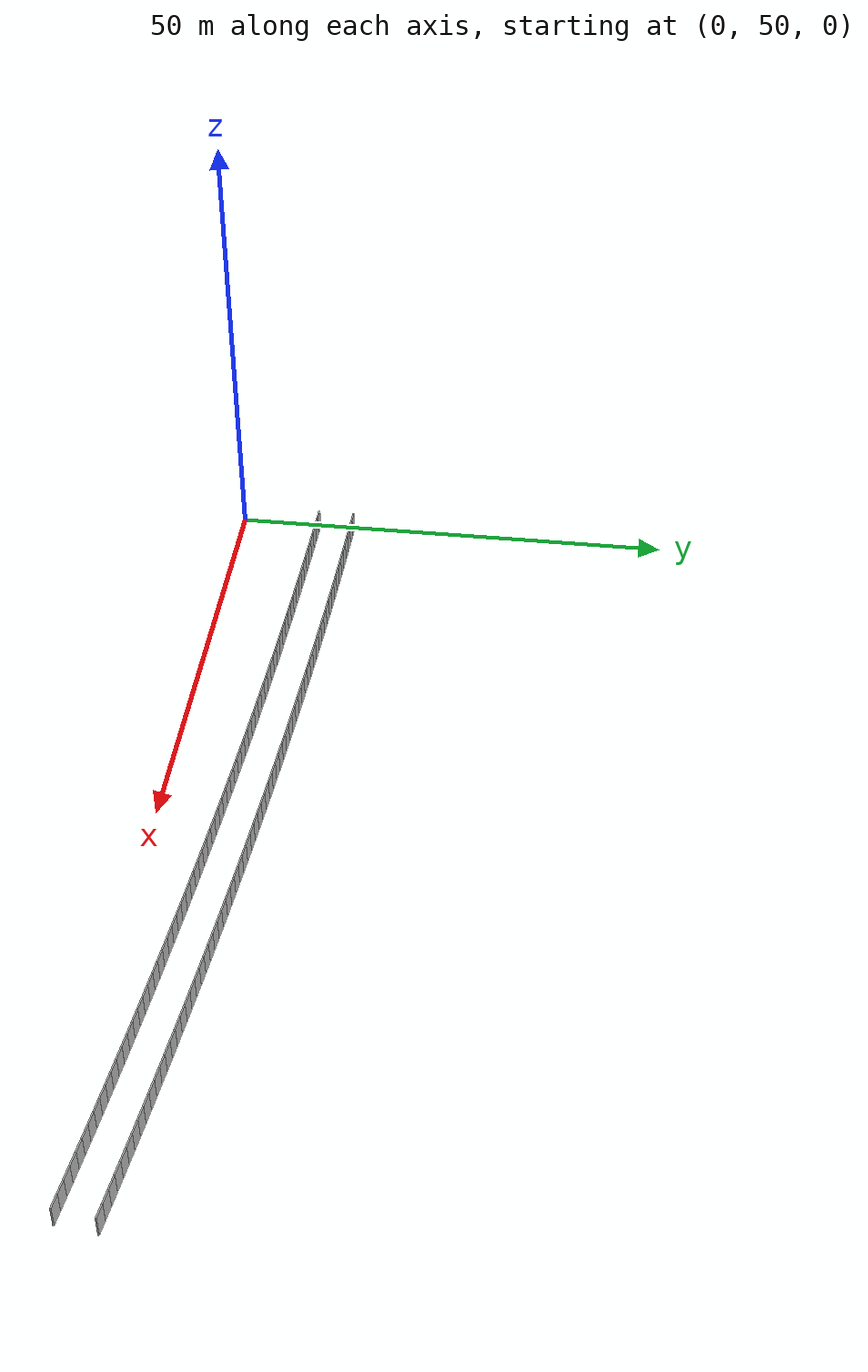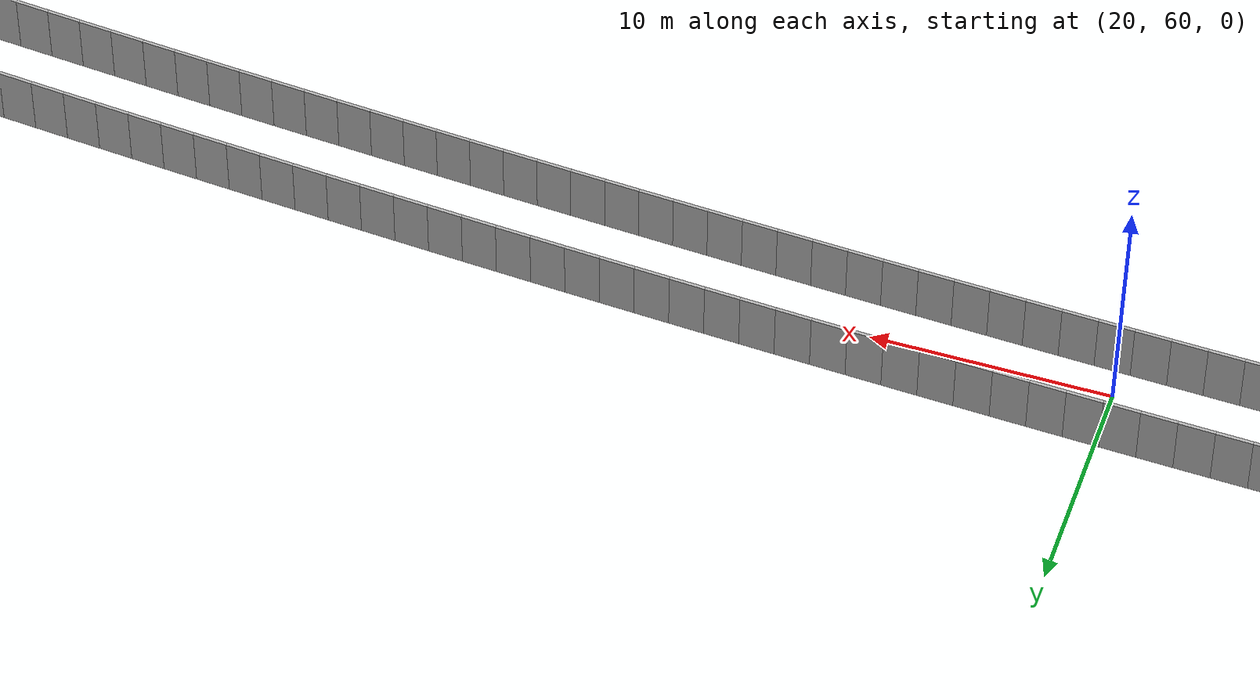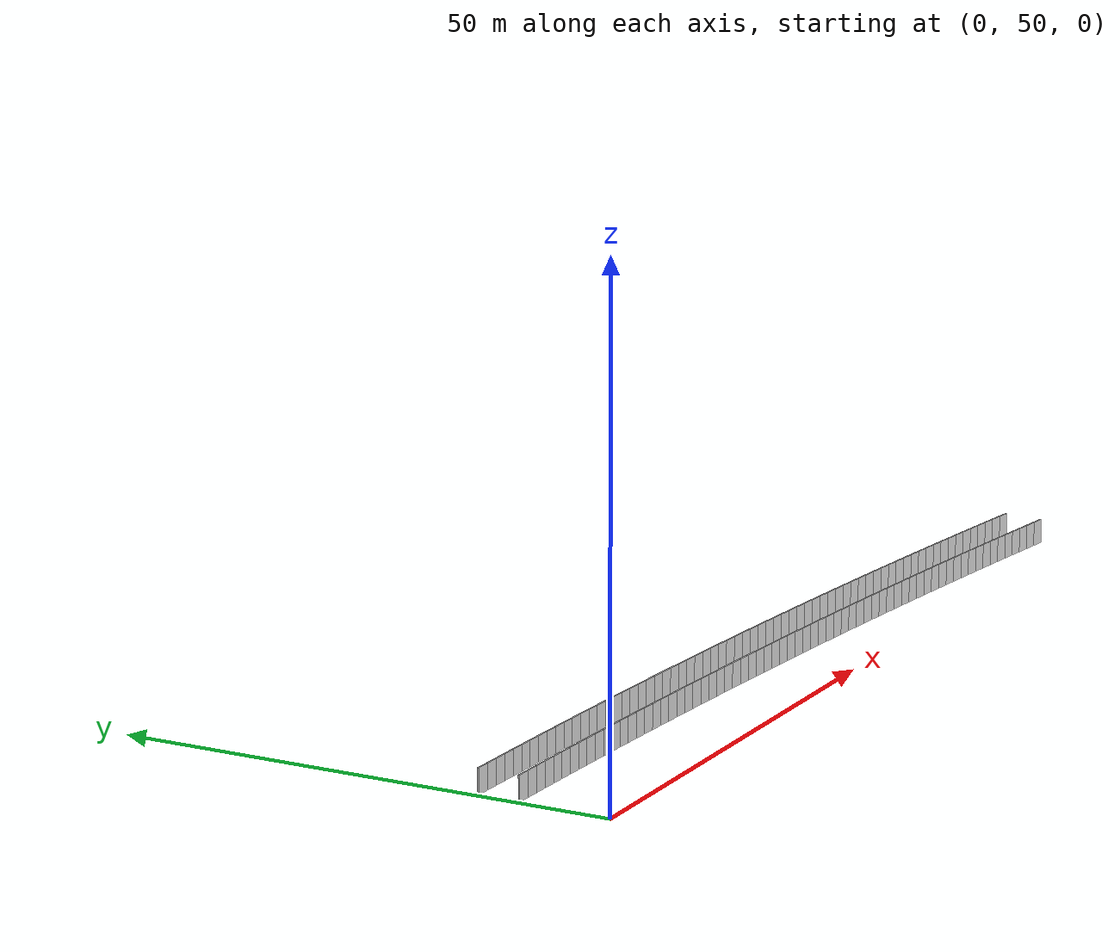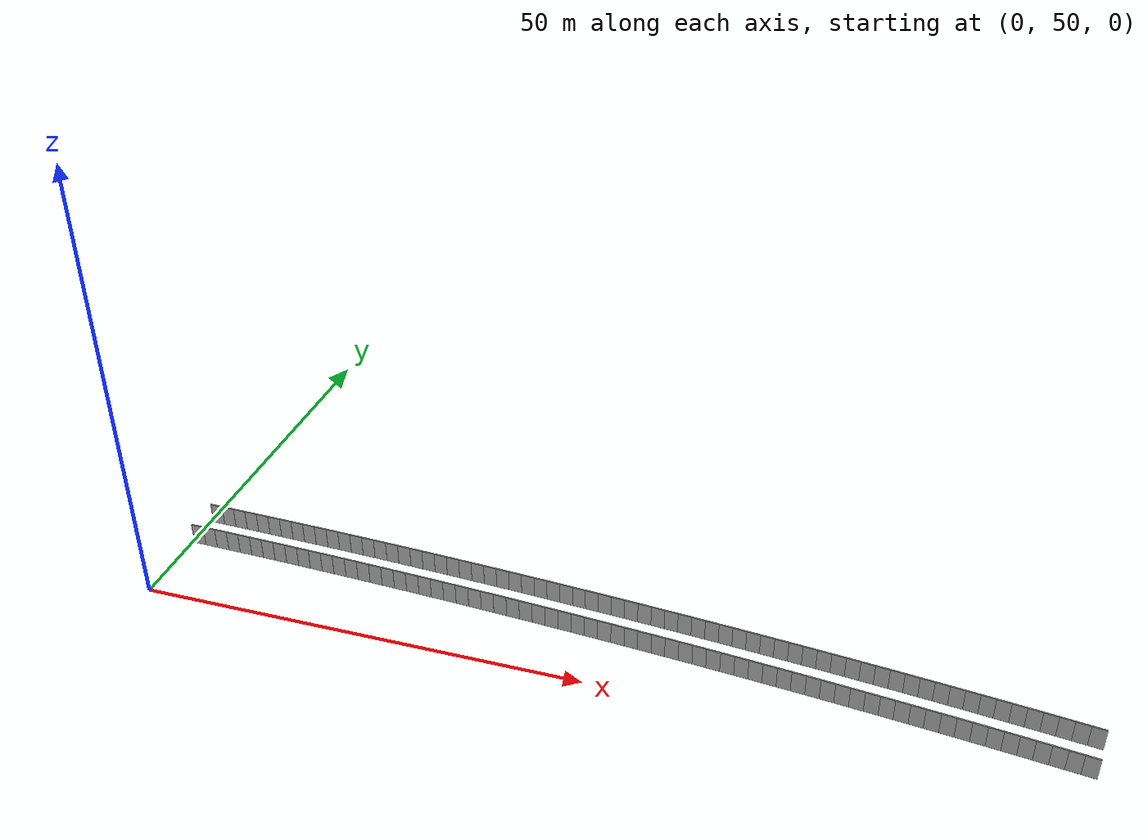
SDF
<?xml version="1.0" ?>
<sdf version="1.6">
  <model name="sps_1223">
    <pose frame="">0 0 0 0 -0 0</pose>
    <static>1</static>
    <self_collide>0</self_collide>
    <allow_auto_disable>0</allow_auto_disable>
    <link name="Wall2825">
      <kinematic>0</kinematic>
      <gravity>1</gravity>
      <self_collide>0</self_collide>
      <collision name="collision">
        <geometry>
          <box>
            <size>1.49657 0.15 2.5</size>
          </box>
        </geometry>
        <pose frame="">0 0 0 0 -0 0</pose>
      </collision>
      <visual name="visual">
        <geometry>
          <box>
            <size>1.49657 0.15 2.5</size>
          </box>
        </geometry>
        <pose frame="">0 0 0 0 -0 0</pose>
        <cast_shadows>1</cast_shadows>
        <transparency>0.0</transparency>
      </visual>
      <pose frame="">99.431 52.0302 1.25 0 -0 3.01741</pose>
    </link>
    <link name="Wall2826">
      <kinematic>0</kinematic>
      <gravity>1</gravity>
      <self_collide>0</self_collide>
      <collision name="collision">
        <geometry>
          <box>
            <size>1.49641 0.15 2.5</size>
          </box>
        </geometry>
        <pose frame="">0 0 0 0 -0 0</pose>
      </collision>
      <visual name="visual">
        <geometry>
          <box>
            <size>1.49641 0.15 2.5</size>
          </box>
        </geometry>
        <pose frame="">0 0 0 0 -0 0</pose>
        <cast_shadows>1</cast_shadows>
        <transparency>0.0</transparency>
      </visual>
      <pose frame="">97.9459 52.2144 1.25 0 -0 3.01896</pose>
    </link>
    <link name="Wall2827">
      <kinematic>0</kinematic>
      <gravity>1</gravity>
      <self_collide>0</self_collide>
      <collision name="collision">
        <geometry>
          <box>
            <size>1.49656 0.15 2.5</size>
          </box>
        </geometry>
        <pose frame="">0 0 0 0 -0 0</pose>
      </collision>
      <visual name="visual">
        <geometry>
          <box>
            <size>1.49656 0.15 2.5</size>
          </box>
        </geometry>
        <pose frame="">0 0 0 0 -0 0</pose>
        <cast_shadows>1</cast_shadows>
        <transparency>0.0</transparency>
      </visual>
      <pose frame="">96.4605 52.3963 1.25 0 -0 3.0205</pose>
    </link>
    <link name="Wall2828">
      <kinematic>0</kinematic>
      <gravity>1</gravity>
      <self_collide>0</self_collide>
      <collision name="collision">
        <geometry>
          <box>
            <size>1.49651 0.15 2.5</size>
          </box>
        </geometry>
        <pose frame="">0 0 0 0 -0 0</pose>
      </collision>
      <visual name="visual">
        <geometry>
          <box>
            <size>1.49651 0.15 2.5</size>
          </box>
        </geometry>
        <pose frame="">0 0 0 0 -0 0</pose>
        <cast_shadows>1</cast_shadows>
        <transparency>0.0</transparency>
      </visual>
      <pose frame="">94.9748 52.5759 1.25 0 -0 3.02209</pose>
    </link>
    <link name="Wall2829">
      <kinematic>0</kinematic>
      <gravity>1</gravity>
      <self_collide>0</self_collide>
      <collision name="collision">
        <geometry>
          <box>
            <size>1.49664 0.15 2.5</size>
          </box>
        </geometry>
        <pose frame="">0 0 0 0 -0 0</pose>
      </collision>
      <visual name="visual">
        <geometry>
          <box>
            <size>1.49664 0.15 2.5</size>
          </box>
        </geometry>
        <pose frame="">0 0 0 0 -0 0</pose>
        <cast_shadows>1</cast_shadows>
        <transparency>0.0</transparency>
      </visual>
      <pose frame="">93.4887 52.7533 1.25 0 -0 3.02346</pose>
    </link>
    <link name="Wall2830">
      <kinematic>0</kinematic>
      <gravity>1</gravity>
      <self_collide>0</self_collide>
      <collision name="collision">
        <geometry>
          <box>
            <size>1.49649 0.15 2.5</size>
          </box>
        </geometry>
        <pose frame="">0 0 0 0 -0 0</pose>
      </collision>
      <visual name="visual">
        <geometry>
          <box>
            <size>1.49649 0.15 2.5</size>
          </box>
        </geometry>
        <pose frame="">0 0 0 0 -0 0</pose>
        <cast_shadows>1</cast_shadows>
        <transparency>0.0</transparency>
      </visual>
      <pose frame="">92.0024 52.9283 1.25 0 -0 3.02534</pose>
    </link>
    <link name="Wall2831">
      <kinematic>0</kinematic>
      <gravity>1</gravity>
      <self_collide>0</self_collide>
      <collision name="collision">
        <geometry>
          <box>
            <size>1.49624 0.15 2.5</size>
          </box>
        </geometry>
        <pose frame="">0 0 0 0 -0 0</pose>
      </collision>
      <visual name="visual">
        <geometry>
          <box>
            <size>1.49624 0.15 2.5</size>
          </box>
        </geometry>
        <pose frame="">0 0 0 0 -0 0</pose>
        <cast_shadows>1</cast_shadows>
        <transparency>0.0</transparency>
      </visual>
      <pose frame="">90.516 53.1008 1.25 0 -0 3.0268</pose>
    </link>
    <link name="Wall2832">
      <kinematic>0</kinematic>
      <gravity>1</gravity>
      <self_collide>0</self_collide>
      <collision name="collision">
        <geometry>
          <box>
            <size>1.49655 0.15 2.5</size>
          </box>
        </geometry>
        <pose frame="">0 0 0 0 -0 0</pose>
      </collision>
      <visual name="visual">
        <geometry>
          <box>
            <size>1.49655 0.15 2.5</size>
          </box>
        </geometry>
        <pose frame="">0 0 0 0 -0 0</pose>
        <cast_shadows>1</cast_shadows>
        <transparency>0.0</transparency>
      </visual>
      <pose frame="">89.0293 53.2709 1.25 0 -0 3.02854</pose>
    </link>
    <link name="Wall2833">
      <kinematic>0</kinematic>
      <gravity>1</gravity>
      <self_collide>0</self_collide>
      <collision name="collision">
        <geometry>
          <box>
            <size>1.49648 0.15 2.5</size>
          </box>
        </geometry>
        <pose frame="">0 0 0 0 -0 0</pose>
      </collision>
      <visual name="visual">
        <geometry>
          <box>
            <size>1.49648 0.15 2.5</size>
          </box>
        </geometry>
        <pose frame="">0 0 0 0 -0 0</pose>
        <cast_shadows>1</cast_shadows>
        <transparency>0.0</transparency>
      </visual>
      <pose frame="">87.5423 53.4386 1.25 0 -0 3.03006</pose>
    </link>
    <link name="Wall2834">
      <kinematic>0</kinematic>
      <gravity>1</gravity>
      <self_collide>0</self_collide>
      <collision name="collision">
        <geometry>
          <box>
            <size>1.49647 0.15 2.5</size>
          </box>
        </geometry>
        <pose frame="">0 0 0 0 -0 0</pose>
      </collision>
      <visual name="visual">
        <geometry>
          <box>
            <size>1.49647 0.15 2.5</size>
          </box>
        </geometry>
        <pose frame="">0 0 0 0 -0 0</pose>
        <cast_shadows>1</cast_shadows>
        <transparency>0.0</transparency>
      </visual>
      <pose frame="">86.055 53.604 1.25 0 -0 3.03162</pose>
    </link>
    <link name="Wall2835">
      <kinematic>0</kinematic>
      <gravity>1</gravity>
      <self_collide>0</self_collide>
      <collision name="collision">
        <geometry>
          <box>
            <size>1.49659 0.15 2.5</size>
          </box>
        </geometry>
        <pose frame="">0 0 0 0 -0 0</pose>
      </collision>
      <visual name="visual">
        <geometry>
          <box>
            <size>1.49659 0.15 2.5</size>
          </box>
        </geometry>
        <pose frame="">0 0 0 0 -0 0</pose>
        <cast_shadows>1</cast_shadows>
        <transparency>0.0</transparency>
      </visual>
      <pose frame="">84.5673 53.7671 1.25 0 -0 3.03314</pose>
    </link>
    <link name="Wall2836">
      <kinematic>0</kinematic>
      <gravity>1</gravity>
      <self_collide>0</self_collide>
      <collision name="collision">
        <geometry>
          <box>
            <size>1.49649 0.15 2.5</size>
          </box>
        </geometry>
        <pose frame="">0 0 0 0 -0 0</pose>
      </collision>
      <visual name="visual">
        <geometry>
          <box>
            <size>1.49649 0.15 2.5</size>
          </box>
        </geometry>
        <pose frame="">0 0 0 0 -0 0</pose>
        <cast_shadows>1</cast_shadows>
        <transparency>0.0</transparency>
      </visual>
      <pose frame="">83.0795 53.9278 1.25 0 -0 3.03486</pose>
    </link>
    <link name="Wall2837">
      <kinematic>0</kinematic>
      <gravity>1</gravity>
      <self_collide>0</self_collide>
      <collision name="collision">
        <geometry>
          <box>
            <size>1.49652 0.15 2.5</size>
          </box>
        </geometry>
        <pose frame="">0 0 0 0 -0 0</pose>
      </collision>
      <visual name="visual">
        <geometry>
          <box>
            <size>1.49652 0.15 2.5</size>
          </box>
        </geometry>
        <pose frame="">0 0 0 0 -0 0</pose>
        <cast_shadows>1</cast_shadows>
        <transparency>0.0</transparency>
      </visual>
      <pose frame="">81.5914 54.0862 1.25 0 -0 3.03625</pose>
    </link>
    <link name="Wall2838">
      <kinematic>0</kinematic>
      <gravity>1</gravity>
      <self_collide>0</self_collide>
      <collision name="collision">
        <geometry>
          <box>
            <size>1.49659 0.15 2.5</size>
          </box>
        </geometry>
        <pose frame="">0 0 0 0 -0 0</pose>
      </collision>
      <visual name="visual">
        <geometry>
          <box>
            <size>1.49659 0.15 2.5</size>
          </box>
        </geometry>
        <pose frame="">0 0 0 0 -0 0</pose>
        <cast_shadows>1</cast_shadows>
        <transparency>0.0</transparency>
      </visual>
      <pose frame="">80.103 54.2422 1.25 0 -0 3.03811</pose>
    </link>
    <link name="Wall2839">
      <kinematic>0</kinematic>
      <gravity>1</gravity>
      <self_collide>0</self_collide>
      <collision name="collision">
        <geometry>
          <box>
            <size>1.49664 0.15 2.5</size>
          </box>
        </geometry>
        <pose frame="">0 0 0 0 -0 0</pose>
      </collision>
      <visual name="visual">
        <geometry>
          <box>
            <size>1.49664 0.15 2.5</size>
          </box>
        </geometry>
        <pose frame="">0 0 0 0 -0 0</pose>
        <cast_shadows>1</cast_shadows>
        <transparency>0.0</transparency>
      </visual>
      <pose frame="">78.6142 54.3958 1.25 0 -0 3.03942</pose>
    </link>
    <link name="Wall2840">
      <kinematic>0</kinematic>
      <gravity>1</gravity>
      <self_collide>0</self_collide>
      <collision name="collision">
        <geometry>
          <box>
            <size>1.4963 0.15 2.5</size>
          </box>
        </geometry>
        <pose frame="">0 0 0 0 -0 0</pose>
      </collision>
      <visual name="visual">
        <geometry>
          <box>
            <size>1.4963 0.15 2.5</size>
          </box>
        </geometry>
        <pose frame="">0 0 0 0 -0 0</pose>
        <cast_shadows>1</cast_shadows>
        <transparency>0.0</transparency>
      </visual>
      <pose frame="">77.1254 54.5471 1.25 0 -0 3.0412</pose>
    </link>
    <link name="Wall2841">
      <kinematic>0</kinematic>
      <gravity>1</gravity>
      <self_collide>0</self_collide>
      <collision name="collision">
        <geometry>
          <box>
            <size>1.49649 0.15 2.5</size>
          </box>
        </geometry>
        <pose frame="">0 0 0 0 -0 0</pose>
      </collision>
      <visual name="visual">
        <geometry>
          <box>
            <size>1.49649 0.15 2.5</size>
          </box>
        </geometry>
        <pose frame="">0 0 0 0 -0 0</pose>
        <cast_shadows>1</cast_shadows>
        <transparency>0.0</transparency>
      </visual>
      <pose frame="">75.6365 54.6959 1.25 0 -0 3.04281</pose>
    </link>
    <link name="Wall2842">
      <kinematic>0</kinematic>
      <gravity>1</gravity>
      <self_collide>0</self_collide>
      <collision name="collision">
        <geometry>
          <box>
            <size>1.49653 0.15 2.5</size>
          </box>
        </geometry>
        <pose frame="">0 0 0 0 -0 0</pose>
      </collision>
      <visual name="visual">
        <geometry>
          <box>
            <size>1.49653 0.15 2.5</size>
          </box>
        </geometry>
        <pose frame="">0 0 0 0 -0 0</pose>
        <cast_shadows>1</cast_shadows>
        <transparency>0.0</transparency>
      </visual>
      <pose frame="">74.1471 54.8424 1.25 0 -0 3.04425</pose>
    </link>
    <link name="Wall2843">
      <kinematic>0</kinematic>
      <gravity>1</gravity>
      <self_collide>0</self_collide>
      <collision name="collision">
        <geometry>
          <box>
            <size>1.49641 0.15 2.5</size>
          </box>
        </geometry>
        <pose frame="">0 0 0 0 -0 0</pose>
      </collision>
      <visual name="visual">
        <geometry>
          <box>
            <size>1.49641 0.15 2.5</size>
          </box>
        </geometry>
        <pose frame="">0 0 0 0 -0 0</pose>
        <cast_shadows>1</cast_shadows>
        <transparency>0.0</transparency>
      </visual>
      <pose frame="">72.6576 54.9866 1.25 0 -0 3.04588</pose>
    </link>
    <link name="Wall2844">
      <kinematic>0</kinematic>
      <gravity>1</gravity>
      <self_collide>0</self_collide>
      <collision name="collision">
        <geometry>
          <box>
            <size>1.49662 0.15 2.5</size>
          </box>
        </geometry>
        <pose frame="">0 0 0 0 -0 0</pose>
      </collision>
      <visual name="visual">
        <geometry>
          <box>
            <size>1.49662 0.15 2.5</size>
          </box>
        </geometry>
        <pose frame="">0 0 0 0 -0 0</pose>
        <cast_shadows>1</cast_shadows>
        <transparency>0.0</transparency>
      </visual>
      <pose frame="">71.1679 55.1285 1.25 0 -0 3.04741</pose>
    </link>
    <link name="Wall2845">
      <kinematic>0</kinematic>
      <gravity>1</gravity>
      <self_collide>0</self_collide>
      <collision name="collision">
        <geometry>
          <box>
            <size>1.49641 0.15 2.5</size>
          </box>
        </geometry>
        <pose frame="">0 0 0 0 -0 0</pose>
      </collision>
      <visual name="visual">
        <geometry>
          <box>
            <size>1.49641 0.15 2.5</size>
          </box>
        </geometry>
        <pose frame="">0 0 0 0 -0 0</pose>
        <cast_shadows>1</cast_shadows>
        <transparency>0.0</transparency>
      </visual>
      <pose frame="">69.6779 55.2681 1.25 0 -0 3.04895</pose>
    </link>
    <link name="Wall2846">
      <kinematic>0</kinematic>
      <gravity>1</gravity>
      <self_collide>0</self_collide>
      <collision name="collision">
        <geometry>
          <box>
            <size>1.49643 0.15 2.5</size>
          </box>
        </geometry>
        <pose frame="">0 0 0 0 -0 0</pose>
      </collision>
      <visual name="visual">
        <geometry>
          <box>
            <size>1.49643 0.15 2.5</size>
          </box>
        </geometry>
        <pose frame="">0 0 0 0 -0 0</pose>
        <cast_shadows>1</cast_shadows>
        <transparency>0.0</transparency>
      </visual>
      <pose frame="">68.1878 55.4053 1.25 0 -0 3.05059</pose>
    </link>
    <link name="Wall2847">
      <kinematic>0</kinematic>
      <gravity>1</gravity>
      <self_collide>0</self_collide>
      <collision name="collision">
        <geometry>
          <box>
            <size>1.49658 0.15 2.5</size>
          </box>
        </geometry>
        <pose frame="">0 0 0 0 -0 0</pose>
      </collision>
      <visual name="visual">
        <geometry>
          <box>
            <size>1.49658 0.15 2.5</size>
          </box>
        </geometry>
        <pose frame="">0 0 0 0 -0 0</pose>
        <cast_shadows>1</cast_shadows>
        <transparency>0.0</transparency>
      </visual>
      <pose frame="">66.6973 55.5401 1.25 0 -0 3.0522</pose>
    </link>
    <link name="Wall2848">
      <kinematic>0</kinematic>
      <gravity>1</gravity>
      <self_collide>0</self_collide>
      <collision name="collision">
        <geometry>
          <box>
            <size>1.49655 0.15 2.5</size>
          </box>
        </geometry>
        <pose frame="">0 0 0 0 -0 0</pose>
      </collision>
      <visual name="visual">
        <geometry>
          <box>
            <size>1.49655 0.15 2.5</size>
          </box>
        </geometry>
        <pose frame="">0 0 0 0 -0 0</pose>
        <cast_shadows>1</cast_shadows>
        <transparency>0.0</transparency>
      </visual>
      <pose frame="">65.2067 55.6725 1.25 0 -0 3.05379</pose>
    </link>
    <link name="Wall2849">
      <kinematic>0</kinematic>
      <gravity>1</gravity>
      <self_collide>0</self_collide>
      <collision name="collision">
        <geometry>
          <box>
            <size>1.49658 0.15 2.5</size>
          </box>
        </geometry>
        <pose frame="">0 0 0 0 -0 0</pose>
      </collision>
      <visual name="visual">
        <geometry>
          <box>
            <size>1.49658 0.15 2.5</size>
          </box>
        </geometry>
        <pose frame="">0 0 0 0 -0 0</pose>
        <cast_shadows>1</cast_shadows>
        <transparency>0.0</transparency>
      </visual>
      <pose frame="">63.7158 55.8025 1.25 0 -0 3.05543</pose>
    </link>
    <link name="Wall2850">
      <kinematic>0</kinematic>
      <gravity>1</gravity>
      <self_collide>0</self_collide>
      <collision name="collision">
        <geometry>
          <box>
            <size>1.49633 0.15 2.5</size>
          </box>
        </geometry>
        <pose frame="">0 0 0 0 -0 0</pose>
      </collision>
      <visual name="visual">
        <geometry>
          <box>
            <size>1.49633 0.15 2.5</size>
          </box>
        </geometry>
        <pose frame="">0 0 0 0 -0 0</pose>
        <cast_shadows>1</cast_shadows>
        <transparency>0.0</transparency>
      </visual>
      <pose frame="">62.2248 55.9302 1.25 0 -0 3.05689</pose>
    </link>
    <link name="Wall2851">
      <kinematic>0</kinematic>
      <gravity>1</gravity>
      <self_collide>0</self_collide>
      <collision name="collision">
        <geometry>
          <box>
            <size>1.49654 0.15 2.5</size>
          </box>
        </geometry>
        <pose frame="">0 0 0 0 -0 0</pose>
      </collision>
      <visual name="visual">
        <geometry>
          <box>
            <size>1.49654 0.15 2.5</size>
          </box>
        </geometry>
        <pose frame="">0 0 0 0 -0 0</pose>
        <cast_shadows>1</cast_shadows>
        <transparency>0.0</transparency>
      </visual>
      <pose frame="">60.7336 56.0555 1.25 0 -0 3.05862</pose>
    </link>
    <link name="Wall2852">
      <kinematic>0</kinematic>
      <gravity>1</gravity>
      <self_collide>0</self_collide>
      <collision name="collision">
        <geometry>
          <box>
            <size>1.4966 0.15 2.5</size>
          </box>
        </geometry>
        <pose frame="">0 0 0 0 -0 0</pose>
      </collision>
      <visual name="visual">
        <geometry>
          <box>
            <size>1.4966 0.15 2.5</size>
          </box>
        </geometry>
        <pose frame="">0 0 0 0 -0 0</pose>
        <cast_shadows>1</cast_shadows>
        <transparency>0.0</transparency>
      </visual>
      <pose frame="">59.2421 56.1784 1.25 0 -0 3.06014</pose>
    </link>
    <link name="Wall2853">
      <kinematic>0</kinematic>
      <gravity>1</gravity>
      <self_collide>0</self_collide>
      <collision name="collision">
        <geometry>
          <box>
            <size>1.49653 0.15 2.5</size>
          </box>
        </geometry>
        <pose frame="">0 0 0 0 -0 0</pose>
      </collision>
      <visual name="visual">
        <geometry>
          <box>
            <size>1.49653 0.15 2.5</size>
          </box>
        </geometry>
        <pose frame="">0 0 0 0 -0 0</pose>
        <cast_shadows>1</cast_shadows>
        <transparency>0.0</transparency>
      </visual>
      <pose frame="">57.7504 56.299 1.25 0 -0 3.06169</pose>
    </link>
    <link name="Wall2854">
      <kinematic>0</kinematic>
      <gravity>1</gravity>
      <self_collide>0</self_collide>
      <collision name="collision">
        <geometry>
          <box>
            <size>1.4964 0.15 2.5</size>
          </box>
        </geometry>
        <pose frame="">0 0 0 0 -0 0</pose>
      </collision>
      <visual name="visual">
        <geometry>
          <box>
            <size>1.4964 0.15 2.5</size>
          </box>
        </geometry>
        <pose frame="">0 0 0 0 -0 0</pose>
        <cast_shadows>1</cast_shadows>
        <transparency>0.0</transparency>
      </visual>
      <pose frame="">56.2586 56.4172 1.25 0 -0 3.06332</pose>
    </link>
    <link name="Wall2855">
      <kinematic>0</kinematic>
      <gravity>1</gravity>
      <self_collide>0</self_collide>
      <collision name="collision">
        <geometry>
          <box>
            <size>1.49659 0.15 2.5</size>
          </box>
        </geometry>
        <pose frame="">0 0 0 0 -0 0</pose>
      </collision>
      <visual name="visual">
        <geometry>
          <box>
            <size>1.49659 0.15 2.5</size>
          </box>
        </geometry>
        <pose frame="">0 0 0 0 -0 0</pose>
        <cast_shadows>1</cast_shadows>
        <transparency>0.0</transparency>
      </visual>
      <pose frame="">54.7666 56.5331 1.25 0 -0 3.06485</pose>
    </link>
    <link name="Wall2856">
      <kinematic>0</kinematic>
      <gravity>1</gravity>
      <self_collide>0</self_collide>
      <collision name="collision">
        <geometry>
          <box>
            <size>1.4964 0.15 2.5</size>
          </box>
        </geometry>
        <pose frame="">0 0 0 0 -0 0</pose>
      </collision>
      <visual name="visual">
        <geometry>
          <box>
            <size>1.4964 0.15 2.5</size>
          </box>
        </geometry>
        <pose frame="">0 0 0 0 -0 0</pose>
        <cast_shadows>1</cast_shadows>
        <transparency>0.0</transparency>
      </visual>
      <pose frame="">53.2744 56.6466 1.25 0 -0 3.06651</pose>
    </link>
    <link name="Wall2857">
      <kinematic>0</kinematic>
      <gravity>1</gravity>
      <self_collide>0</self_collide>
      <collision name="collision">
        <geometry>
          <box>
            <size>1.49648 0.15 2.5</size>
          </box>
        </geometry>
        <pose frame="">0 0 0 0 -0 0</pose>
      </collision>
      <visual name="visual">
        <geometry>
          <box>
            <size>1.49648 0.15 2.5</size>
          </box>
        </geometry>
        <pose frame="">0 0 0 0 -0 0</pose>
        <cast_shadows>1</cast_shadows>
        <transparency>0.0</transparency>
      </visual>
      <pose frame="">51.7821 56.7577 1.25 0 -0 3.06803</pose>
    </link>
    <link name="Wall2858">
      <kinematic>0</kinematic>
      <gravity>1</gravity>
      <self_collide>0</self_collide>
      <collision name="collision">
        <geometry>
          <box>
            <size>1.49648 0.15 2.5</size>
          </box>
        </geometry>
        <pose frame="">0 0 0 0 -0 0</pose>
      </collision>
      <visual name="visual">
        <geometry>
          <box>
            <size>1.49648 0.15 2.5</size>
          </box>
        </geometry>
        <pose frame="">0 0 0 0 -0 0</pose>
        <cast_shadows>1</cast_shadows>
        <transparency>0.0</transparency>
      </visual>
      <pose frame="">50.2895 56.8664 1.25 0 -0 3.06975</pose>
    </link>
    <link name="Wall2859">
      <kinematic>0</kinematic>
      <gravity>1</gravity>
      <self_collide>0</self_collide>
      <collision name="collision">
        <geometry>
          <box>
            <size>1.49651 0.15 2.5</size>
          </box>
        </geometry>
        <pose frame="">0 0 0 0 -0 0</pose>
      </collision>
      <visual name="visual">
        <geometry>
          <box>
            <size>1.49651 0.15 2.5</size>
          </box>
        </geometry>
        <pose frame="">0 0 0 0 -0 0</pose>
        <cast_shadows>1</cast_shadows>
        <transparency>0.0</transparency>
      </visual>
      <pose frame="">48.7968 56.9728 1.25 0 -0 3.07114</pose>
    </link>
    <link name="Wall2860">
      <kinematic>0</kinematic>
      <gravity>1</gravity>
      <self_collide>0</self_collide>
      <collision name="collision">
        <geometry>
          <box>
            <size>1.49653 0.15 2.5</size>
          </box>
        </geometry>
        <pose frame="">0 0 0 0 -0 0</pose>
      </collision>
      <visual name="visual">
        <geometry>
          <box>
            <size>1.49653 0.15 2.5</size>
          </box>
        </geometry>
        <pose frame="">0 0 0 0 -0 0</pose>
        <cast_shadows>1</cast_shadows>
        <transparency>0.0</transparency>
      </visual>
      <pose frame="">47.3039 57.077 1.25 0 -0 3.07269</pose>
    </link>
    <link name="Wall2861">
      <kinematic>0</kinematic>
      <gravity>1</gravity>
      <self_collide>0</self_collide>
      <collision name="collision">
        <geometry>
          <box>
            <size>1.4966 0.15 2.5</size>
          </box>
        </geometry>
        <pose frame="">0 0 0 0 -0 0</pose>
      </collision>
      <visual name="visual">
        <geometry>
          <box>
            <size>1.4966 0.15 2.5</size>
          </box>
        </geometry>
        <pose frame="">0 0 0 0 -0 0</pose>
        <cast_shadows>1</cast_shadows>
        <transparency>0.0</transparency>
      </visual>
      <pose frame="">45.8108 57.1787 1.25 0 -0 3.07445</pose>
    </link>
    <link name="Wall2862">
      <kinematic>0</kinematic>
      <gravity>1</gravity>
      <self_collide>0</self_collide>
      <collision name="collision">
        <geometry>
          <box>
            <size>1.49639 0.15 2.5</size>
          </box>
        </geometry>
        <pose frame="">0 0 0 0 -0 0</pose>
      </collision>
      <visual name="visual">
        <geometry>
          <box>
            <size>1.49639 0.15 2.5</size>
          </box>
        </geometry>
        <pose frame="">0 0 0 0 -0 0</pose>
        <cast_shadows>1</cast_shadows>
        <transparency>0.0</transparency>
      </visual>
      <pose frame="">44.3176 57.278 1.25 0 -0 3.07592</pose>
    </link>
    <link name="Wall2863">
      <kinematic>0</kinematic>
      <gravity>1</gravity>
      <self_collide>0</self_collide>
      <collision name="collision">
        <geometry>
          <box>
            <size>1.49648 0.15 2.5</size>
          </box>
        </geometry>
        <pose frame="">0 0 0 0 -0 0</pose>
      </collision>
      <visual name="visual">
        <geometry>
          <box>
            <size>1.49648 0.15 2.5</size>
          </box>
        </geometry>
        <pose frame="">0 0 0 0 -0 0</pose>
        <cast_shadows>1</cast_shadows>
        <transparency>0.0</transparency>
      </visual>
      <pose frame="">42.8244 57.375 1.25 0 -0 3.07756</pose>
    </link>
    <link name="Wall2864">
      <kinematic>0</kinematic>
      <gravity>1</gravity>
      <self_collide>0</self_collide>
      <collision name="collision">
        <geometry>
          <box>
            <size>1.49651 0.15 2.5</size>
          </box>
        </geometry>
        <pose frame="">0 0 0 0 -0 0</pose>
      </collision>
      <visual name="visual">
        <geometry>
          <box>
            <size>1.49651 0.15 2.5</size>
          </box>
        </geometry>
        <pose frame="">0 0 0 0 -0 0</pose>
        <cast_shadows>1</cast_shadows>
        <transparency>0.0</transparency>
      </visual>
      <pose frame="">41.3309 57.4696 1.25 0 -0 3.07911</pose>
    </link>
    <link name="Wall2865">
      <kinematic>0</kinematic>
      <gravity>1</gravity>
      <self_collide>0</self_collide>
      <collision name="collision">
        <geometry>
          <box>
            <size>1.4966 0.15 2.5</size>
          </box>
        </geometry>
        <pose frame="">0 0 0 0 -0 0</pose>
      </collision>
      <visual name="visual">
        <geometry>
          <box>
            <size>1.4966 0.15 2.5</size>
          </box>
        </geometry>
        <pose frame="">0 0 0 0 -0 0</pose>
        <cast_shadows>1</cast_shadows>
        <transparency>0.0</transparency>
      </visual>
      <pose frame="">39.8371 57.5618 1.25 0 -0 3.08075</pose>
    </link>
    <link name="Wall2866">
      <kinematic>0</kinematic>
      <gravity>1</gravity>
      <self_collide>0</self_collide>
      <collision name="collision">
        <geometry>
          <box>
            <size>1.4964 0.15 2.5</size>
          </box>
        </geometry>
        <pose frame="">0 0 0 0 -0 0</pose>
      </collision>
      <visual name="visual">
        <geometry>
          <box>
            <size>1.4964 0.15 2.5</size>
          </box>
        </geometry>
        <pose frame="">0 0 0 0 -0 0</pose>
        <cast_shadows>1</cast_shadows>
        <transparency>0.0</transparency>
      </visual>
      <pose frame="">38.3433 57.6516 1.25 0 -0 3.08237</pose>
    </link>
    <link name="Wall2867">
      <kinematic>0</kinematic>
      <gravity>1</gravity>
      <self_collide>0</self_collide>
      <collision name="collision">
        <geometry>
          <box>
            <size>1.49652 0.15 2.5</size>
          </box>
        </geometry>
        <pose frame="">0 0 0 0 -0 0</pose>
      </collision>
      <visual name="visual">
        <geometry>
          <box>
            <size>1.49652 0.15 2.5</size>
          </box>
        </geometry>
        <pose frame="">0 0 0 0 -0 0</pose>
        <cast_shadows>1</cast_shadows>
        <transparency>0.0</transparency>
      </visual>
      <pose frame="">36.8494 57.7391 1.25 0 -0 3.08381</pose>
    </link>
    <link name="Wall2868">
      <kinematic>0</kinematic>
      <gravity>1</gravity>
      <self_collide>0</self_collide>
      <collision name="collision">
        <geometry>
          <box>
            <size>1.49631 0.15 2.5</size>
          </box>
        </geometry>
        <pose frame="">0 0 0 0 -0 0</pose>
      </collision>
      <visual name="visual">
        <geometry>
          <box>
            <size>1.49631 0.15 2.5</size>
          </box>
        </geometry>
        <pose frame="">0 0 0 0 -0 0</pose>
        <cast_shadows>1</cast_shadows>
        <transparency>0.0</transparency>
      </visual>
      <pose frame="">35.3555 57.8242 1.25 0 -0 3.08556</pose>
    </link>
    <link name="Wall2869">
      <kinematic>0</kinematic>
      <gravity>1</gravity>
      <self_collide>0</self_collide>
      <collision name="collision">
        <geometry>
          <box>
            <size>1.49667 0.15 2.5</size>
          </box>
        </geometry>
        <pose frame="">0 0 0 0 -0 0</pose>
      </collision>
      <visual name="visual">
        <geometry>
          <box>
            <size>1.49667 0.15 2.5</size>
          </box>
        </geometry>
        <pose frame="">0 0 0 0 -0 0</pose>
        <cast_shadows>1</cast_shadows>
        <transparency>0.0</transparency>
      </visual>
      <pose frame="">33.8613 57.9069 1.25 0 -0 3.08704</pose>
    </link>
    <link name="Wall2870">
      <kinematic>0</kinematic>
      <gravity>1</gravity>
      <self_collide>0</self_collide>
      <collision name="collision">
        <geometry>
          <box>
            <size>1.49648 0.15 2.5</size>
          </box>
        </geometry>
        <pose frame="">0 0 0 0 -0 0</pose>
      </collision>
      <visual name="visual">
        <geometry>
          <box>
            <size>1.49648 0.15 2.5</size>
          </box>
        </geometry>
        <pose frame="">0 0 0 0 -0 0</pose>
        <cast_shadows>1</cast_shadows>
        <transparency>0.0</transparency>
      </visual>
      <pose frame="">32.3668 57.9873 1.25 0 -0 3.08867</pose>
    </link>
    <link name="Wall2871">
      <kinematic>0</kinematic>
      <gravity>1</gravity>
      <self_collide>0</self_collide>
      <collision name="collision">
        <geometry>
          <box>
            <size>1.49654 0.15 2.5</size>
          </box>
        </geometry>
        <pose frame="">0 0 0 0 -0 0</pose>
      </collision>
      <visual name="visual">
        <geometry>
          <box>
            <size>1.49654 0.15 2.5</size>
          </box>
        </geometry>
        <pose frame="">0 0 0 0 -0 0</pose>
        <cast_shadows>1</cast_shadows>
        <transparency>0.0</transparency>
      </visual>
      <pose frame="">30.8724 58.0653 1.25 0 -0 3.09022</pose>
    </link>
    <link name="Wall2872">
      <kinematic>0</kinematic>
      <gravity>1</gravity>
      <self_collide>0</self_collide>
      <collision name="collision">
        <geometry>
          <box>
            <size>1.49649 0.15 2.5</size>
          </box>
        </geometry>
        <pose frame="">0 0 0 0 -0 0</pose>
      </collision>
      <visual name="visual">
        <geometry>
          <box>
            <size>1.49649 0.15 2.5</size>
          </box>
        </geometry>
        <pose frame="">0 0 0 0 -0 0</pose>
        <cast_shadows>1</cast_shadows>
        <transparency>0.0</transparency>
      </visual>
      <pose frame="">29.3778 58.141 1.25 0 -0 3.09173</pose>
    </link>
    <link name="Wall2873">
      <kinematic>0</kinematic>
      <gravity>1</gravity>
      <self_collide>0</self_collide>
      <collision name="collision">
        <geometry>
          <box>
            <size>1.49655 0.15 2.5</size>
          </box>
        </geometry>
        <pose frame="">0 0 0 0 -0 0</pose>
      </collision>
      <visual name="visual">
        <geometry>
          <box>
            <size>1.49655 0.15 2.5</size>
          </box>
        </geometry>
        <pose frame="">0 0 0 0 -0 0</pose>
        <cast_shadows>1</cast_shadows>
        <transparency>0.0</transparency>
      </visual>
      <pose frame="">27.883 58.2143 1.25 0 -0 3.09345</pose>
    </link>
    <link name="Wall2874">
      <kinematic>0</kinematic>
      <gravity>1</gravity>
      <self_collide>0</self_collide>
      <collision name="collision">
        <geometry>
          <box>
            <size>1.49644 0.15 2.5</size>
          </box>
        </geometry>
        <pose frame="">0 0 0 0 -0 0</pose>
      </collision>
      <visual name="visual">
        <geometry>
          <box>
            <size>1.49644 0.15 2.5</size>
          </box>
        </geometry>
        <pose frame="">0 0 0 0 -0 0</pose>
        <cast_shadows>1</cast_shadows>
        <transparency>0.0</transparency>
      </visual>
      <pose frame="">26.3882 58.2852 1.25 0 -0 3.09496</pose>
    </link>
    <link name="Wall2875">
      <kinematic>0</kinematic>
      <gravity>1</gravity>
      <self_collide>0</self_collide>
      <collision name="collision">
        <geometry>
          <box>
            <size>1.49651 0.15 2.5</size>
          </box>
        </geometry>
        <pose frame="">0 0 0 0 -0 0</pose>
      </collision>
      <visual name="visual">
        <geometry>
          <box>
            <size>1.49651 0.15 2.5</size>
          </box>
        </geometry>
        <pose frame="">0 0 0 0 -0 0</pose>
        <cast_shadows>1</cast_shadows>
        <transparency>0.0</transparency>
      </visual>
      <pose frame="">24.8933 58.3538 1.25 0 -0 3.09655</pose>
    </link>
    <link name="Wall2876">
      <kinematic>0</kinematic>
      <gravity>1</gravity>
      <self_collide>0</self_collide>
      <collision name="collision">
        <geometry>
          <box>
            <size>1.49658 0.15 2.5</size>
          </box>
        </geometry>
        <pose frame="">0 0 0 0 -0 0</pose>
      </collision>
      <visual name="visual">
        <geometry>
          <box>
            <size>1.49658 0.15 2.5</size>
          </box>
        </geometry>
        <pose frame="">0 0 0 0 -0 0</pose>
        <cast_shadows>1</cast_shadows>
        <transparency>0.0</transparency>
      </visual>
      <pose frame="">23.3982 58.4199 1.25 0 -0 3.09827</pose>
    </link>
    <link name="Wall2877">
      <kinematic>0</kinematic>
      <gravity>1</gravity>
      <self_collide>0</self_collide>
      <collision name="collision">
        <geometry>
          <box>
            <size>1.49649 0.15 2.5</size>
          </box>
        </geometry>
        <pose frame="">0 0 0 0 -0 0</pose>
      </collision>
      <visual name="visual">
        <geometry>
          <box>
            <size>1.49649 0.15 2.5</size>
          </box>
        </geometry>
        <pose frame="">0 0 0 0 -0 0</pose>
        <cast_shadows>1</cast_shadows>
        <transparency>0.0</transparency>
      </visual>
      <pose frame="">21.9031 58.4836 1.25 0 -0 3.09973</pose>
    </link>
    <link name="Wall2878">
      <kinematic>0</kinematic>
      <gravity>1</gravity>
      <self_collide>0</self_collide>
      <collision name="collision">
        <geometry>
          <box>
            <size>1.49645 0.15 2.5</size>
          </box>
        </geometry>
        <pose frame="">0 0 0 0 -0 0</pose>
      </collision>
      <visual name="visual">
        <geometry>
          <box>
            <size>1.49645 0.15 2.5</size>
          </box>
        </geometry>
        <pose frame="">0 0 0 0 -0 0</pose>
        <cast_shadows>1</cast_shadows>
        <transparency>0.0</transparency>
      </visual>
      <pose frame="">20.4079 58.545 1.25 0 -0 3.10137</pose>
    </link>
    <link name="Wall2879">
      <kinematic>0</kinematic>
      <gravity>1</gravity>
      <self_collide>0</self_collide>
      <collision name="collision">
        <geometry>
          <box>
            <size>1.49649 0.15 2.5</size>
          </box>
        </geometry>
        <pose frame="">0 0 0 0 -0 0</pose>
      </collision>
      <visual name="visual">
        <geometry>
          <box>
            <size>1.49649 0.15 2.5</size>
          </box>
        </geometry>
        <pose frame="">0 0 0 0 -0 0</pose>
        <cast_shadows>1</cast_shadows>
        <transparency>0.0</transparency>
      </visual>
      <pose frame="">18.9126 58.6041 1.25 0 -0 3.10284</pose>
    </link>
    <link name="Wall2880">
      <kinematic>0</kinematic>
      <gravity>1</gravity>
      <self_collide>0</self_collide>
      <collision name="collision">
        <geometry>
          <box>
            <size>1.49645 0.15 2.5</size>
          </box>
        </geometry>
        <pose frame="">0 0 0 0 -0 0</pose>
      </collision>
      <visual name="visual">
        <geometry>
          <box>
            <size>1.49645 0.15 2.5</size>
          </box>
        </geometry>
        <pose frame="">0 0 0 0 -0 0</pose>
        <cast_shadows>1</cast_shadows>
        <transparency>0.0</transparency>
      </visual>
      <pose frame="">17.4172 58.6608 1.25 0 -0 3.10455</pose>
    </link>
    <link name="Wall2881">
      <kinematic>0</kinematic>
      <gravity>1</gravity>
      <self_collide>0</self_collide>
      <collision name="collision">
        <geometry>
          <box>
            <size>1.49655 0.15 2.5</size>
          </box>
        </geometry>
        <pose frame="">0 0 0 0 -0 0</pose>
      </collision>
      <visual name="visual">
        <geometry>
          <box>
            <size>1.49655 0.15 2.5</size>
          </box>
        </geometry>
        <pose frame="">0 0 0 0 -0 0</pose>
        <cast_shadows>1</cast_shadows>
        <transparency>0.0</transparency>
      </visual>
      <pose frame="">15.9217 58.7151 1.25 0 -0 3.10602</pose>
    </link>
    <link name="Wall2882">
      <kinematic>0</kinematic>
      <gravity>1</gravity>
      <self_collide>0</self_collide>
      <collision name="collision">
        <geometry>
          <box>
            <size>1.49647 0.15 2.5</size>
          </box>
        </geometry>
        <pose frame="">0 0 0 0 -0 0</pose>
      </collision>
      <visual name="visual">
        <geometry>
          <box>
            <size>1.49647 0.15 2.5</size>
          </box>
        </geometry>
        <pose frame="">0 0 0 0 -0 0</pose>
        <cast_shadows>1</cast_shadows>
        <transparency>0.0</transparency>
      </visual>
      <pose frame="">14.426 58.7671 1.25 0 -0 3.10765</pose>
    </link>
    <link name="Wall2883">
      <kinematic>0</kinematic>
      <gravity>1</gravity>
      <self_collide>0</self_collide>
      <collision name="collision">
        <geometry>
          <box>
            <size>1.49657 0.15 2.5</size>
          </box>
        </geometry>
        <pose frame="">0 0 0 0 -0 0</pose>
      </collision>
      <visual name="visual">
        <geometry>
          <box>
            <size>1.49657 0.15 2.5</size>
          </box>
        </geometry>
        <pose frame="">0 0 0 0 -0 0</pose>
        <cast_shadows>1</cast_shadows>
        <transparency>0.0</transparency>
      </visual>
      <pose frame="">12.9304 58.8167 1.25 0 -0 3.10925</pose>
    </link>
    <link name="Wall2884">
      <kinematic>0</kinematic>
      <gravity>1</gravity>
      <self_collide>0</self_collide>
      <collision name="collision">
        <geometry>
          <box>
            <size>1.4965 0.15 2.5</size>
          </box>
        </geometry>
        <pose frame="">0 0 0 0 -0 0</pose>
      </collision>
      <visual name="visual">
        <geometry>
          <box>
            <size>1.4965 0.15 2.5</size>
          </box>
        </geometry>
        <pose frame="">0 0 0 0 -0 0</pose>
        <cast_shadows>1</cast_shadows>
        <transparency>0.0</transparency>
      </visual>
      <pose frame="">11.4346 58.8639 1.25 0 -0 3.11084</pose>
    </link>
    <link name="Wall2885">
      <kinematic>0</kinematic>
      <gravity>1</gravity>
      <self_collide>0</self_collide>
      <collision name="collision">
        <geometry>
          <box>
            <size>1.49642 0.15 2.5</size>
          </box>
        </geometry>
        <pose frame="">0 0 0 0 -0 0</pose>
      </collision>
      <visual name="visual">
        <geometry>
          <box>
            <size>1.49642 0.15 2.5</size>
          </box>
        </geometry>
        <pose frame="">0 0 0 0 -0 0</pose>
        <cast_shadows>1</cast_shadows>
        <transparency>0.0</transparency>
      </visual>
      <pose frame="">9.93877 58.9087 1.25 0 -0 3.11247</pose>
    </link>
    <link name="Wall2886">
      <kinematic>0</kinematic>
      <gravity>1</gravity>
      <self_collide>0</self_collide>
      <collision name="collision">
        <geometry>
          <box>
            <size>1.49642 0.15 2.5</size>
          </box>
        </geometry>
        <pose frame="">0 0 0 0 -0 0</pose>
      </collision>
      <visual name="visual">
        <geometry>
          <box>
            <size>1.49642 0.15 2.5</size>
          </box>
        </geometry>
        <pose frame="">0 0 0 0 -0 0</pose>
        <cast_shadows>1</cast_shadows>
        <transparency>0.0</transparency>
      </visual>
      <pose frame="">8.44295 58.9512 1.25 0 -0 3.11394</pose>
    </link>
    <link name="Wall2887">
      <kinematic>0</kinematic>
      <gravity>1</gravity>
      <self_collide>0</self_collide>
      <collision name="collision">
        <geometry>
          <box>
            <size>1.49666 0.15 2.5</size>
          </box>
        </geometry>
        <pose frame="">0 0 0 0 -0 0</pose>
      </collision>
      <visual name="visual">
        <geometry>
          <box>
            <size>1.49666 0.15 2.5</size>
          </box>
        </geometry>
        <pose frame="">0 0 0 0 -0 0</pose>
        <cast_shadows>1</cast_shadows>
        <transparency>0.0</transparency>
      </visual>
      <pose frame="">6.94695 58.9913 1.25 0 -0 3.11565</pose>
    </link>
    <link name="Wall2888">
      <kinematic>0</kinematic>
      <gravity>1</gravity>
      <self_collide>0</self_collide>
      <collision name="collision">
        <geometry>
          <box>
            <size>1.49648 0.15 2.5</size>
          </box>
        </geometry>
        <pose frame="">0 0 0 0 -0 0</pose>
      </collision>
      <visual name="visual">
        <geometry>
          <box>
            <size>1.49648 0.15 2.5</size>
          </box>
        </geometry>
        <pose frame="">0 0 0 0 -0 0</pose>
        <cast_shadows>1</cast_shadows>
        <transparency>0.0</transparency>
      </visual>
      <pose frame="">5.45086 59.029 1.25 0 -0 3.11712</pose>
    </link>
    <link name="Wall2889">
      <kinematic>0</kinematic>
      <gravity>1</gravity>
      <self_collide>0</self_collide>
      <collision name="collision">
        <geometry>
          <box>
            <size>1.49636 0.15 2.5</size>
          </box>
        </geometry>
        <pose frame="">0 0 0 0 -0 0</pose>
      </collision>
      <visual name="visual">
        <geometry>
          <box>
            <size>1.49636 0.15 2.5</size>
          </box>
        </geometry>
        <pose frame="">0 0 0 0 -0 0</pose>
        <cast_shadows>1</cast_shadows>
        <transparency>0.0</transparency>
      </visual>
      <pose frame="">3.95486 59.0643 1.25 0 -0 3.11887</pose>
    </link>
    <link name="Wall2890">
      <kinematic>0</kinematic>
      <gravity>1</gravity>
      <self_collide>0</self_collide>
      <collision name="collision">
        <geometry>
          <box>
            <size>1.49656 0.15 2.5</size>
          </box>
        </geometry>
        <pose frame="">0 0 0 0 -0 0</pose>
      </collision>
      <visual name="visual">
        <geometry>
          <box>
            <size>1.49656 0.15 2.5</size>
          </box>
        </geometry>
        <pose frame="">0 0 0 0 -0 0</pose>
        <cast_shadows>1</cast_shadows>
        <transparency>0.0</transparency>
      </visual>
      <pose frame="">2.45876 59.0973 1.25 0 -0 3.12022</pose>
    </link>
    <link name="Wall2891">
      <kinematic>0</kinematic>
      <gravity>1</gravity>
      <self_collide>0</self_collide>
      <collision name="collision">
        <geometry>
          <box>
            <size>1.49651 0.15 2.5</size>
          </box>
        </geometry>
        <pose frame="">0 0 0 0 -0 0</pose>
      </collision>
      <visual name="visual">
        <geometry>
          <box>
            <size>1.49651 0.15 2.5</size>
          </box>
        </geometry>
        <pose frame="">0 0 0 0 -0 0</pose>
        <cast_shadows>1</cast_shadows>
        <transparency>0.0</transparency>
      </visual>
      <pose frame="">0.962547 59.128 1.25 0 -0 3.12193</pose>
    </link>
    <link name="Wall5436">
      <kinematic>0</kinematic>
      <gravity>1</gravity>
      <self_collide>0</self_collide>
      <collision name="collision">
        <geometry>
          <box>
            <size>1.50297 0.15 2.5</size>
          </box>
        </geometry>
        <pose frame="">0 0 0 0 -0 0</pose>
      </collision>
      <visual name="visual">
        <geometry>
          <box>
            <size>1.50297 0.15 2.5</size>
          </box>
        </geometry>
        <pose frame="">0 0 0 0 -0 0</pose>
        <cast_shadows>1</cast_shadows>
        <transparency>0.0</transparency>
      </visual>
      <pose frame="">99.9435 56.138 1.25 0 -0 3.01737</pose>
    </link>
    <link name="Wall5437">
      <kinematic>0</kinematic>
      <gravity>1</gravity>
      <self_collide>0</self_collide>
      <collision name="collision">
        <geometry>
          <box>
            <size>1.50307 0.15 2.5</size>
          </box>
        </geometry>
        <pose frame="">0 0 0 0 -0 0</pose>
      </collision>
      <visual name="visual">
        <geometry>
          <box>
            <size>1.50307 0.15 2.5</size>
          </box>
        </geometry>
        <pose frame="">0 0 0 0 -0 0</pose>
        <cast_shadows>1</cast_shadows>
        <transparency>0.0</transparency>
      </visual>
      <pose frame="">98.452 56.3231 1.25 0 -0 3.01885</pose>
    </link>
    <link name="Wall5438">
      <kinematic>0</kinematic>
      <gravity>1</gravity>
      <self_collide>0</self_collide>
      <collision name="collision">
        <geometry>
          <box>
            <size>1.50323 0.15 2.5</size>
          </box>
        </geometry>
        <pose frame="">0 0 0 0 -0 0</pose>
      </collision>
      <visual name="visual">
        <geometry>
          <box>
            <size>1.50323 0.15 2.5</size>
          </box>
        </geometry>
        <pose frame="">0 0 0 0 -0 0</pose>
        <cast_shadows>1</cast_shadows>
        <transparency>0.0</transparency>
      </visual>
      <pose frame="">96.96 56.5058 1.25 0 -0 3.02063</pose>
    </link>
    <link name="Wall5439">
      <kinematic>0</kinematic>
      <gravity>1</gravity>
      <self_collide>0</self_collide>
      <collision name="collision">
        <geometry>
          <box>
            <size>1.50306 0.15 2.5</size>
          </box>
        </geometry>
        <pose frame="">0 0 0 0 -0 0</pose>
      </collision>
      <visual name="visual">
        <geometry>
          <box>
            <size>1.50306 0.15 2.5</size>
          </box>
        </geometry>
        <pose frame="">0 0 0 0 -0 0</pose>
        <cast_shadows>1</cast_shadows>
        <transparency>0.0</transparency>
      </visual>
      <pose frame="">95.4676 56.686 1.25 0 -0 3.02225</pose>
    </link>
    <link name="Wall5440">
      <kinematic>0</kinematic>
      <gravity>1</gravity>
      <self_collide>0</self_collide>
      <collision name="collision">
        <geometry>
          <box>
            <size>1.50307 0.15 2.5</size>
          </box>
        </geometry>
        <pose frame="">0 0 0 0 -0 0</pose>
      </collision>
      <visual name="visual">
        <geometry>
          <box>
            <size>1.50307 0.15 2.5</size>
          </box>
        </geometry>
        <pose frame="">0 0 0 0 -0 0</pose>
        <cast_shadows>1</cast_shadows>
        <transparency>0.0</transparency>
      </visual>
      <pose frame="">93.9752 56.864 1.25 0 -0 3.02356</pose>
    </link>
    <link name="Wall5441">
      <kinematic>0</kinematic>
      <gravity>1</gravity>
      <self_collide>0</self_collide>
      <collision name="collision">
        <geometry>
          <box>
            <size>1.50296 0.15 2.5</size>
          </box>
        </geometry>
        <pose frame="">0 0 0 0 -0 0</pose>
      </collision>
      <visual name="visual">
        <geometry>
          <box>
            <size>1.50296 0.15 2.5</size>
          </box>
        </geometry>
        <pose frame="">0 0 0 0 -0 0</pose>
        <cast_shadows>1</cast_shadows>
        <transparency>0.0</transparency>
      </visual>
      <pose frame="">92.4824 57.0397 1.25 0 -0 3.02527</pose>
    </link>
    <link name="Wall5442">
      <kinematic>0</kinematic>
      <gravity>1</gravity>
      <self_collide>0</self_collide>
      <collision name="collision">
        <geometry>
          <box>
            <size>1.50306 0.15 2.5</size>
          </box>
        </geometry>
        <pose frame="">0 0 0 0 -0 0</pose>
      </collision>
      <visual name="visual">
        <geometry>
          <box>
            <size>1.50306 0.15 2.5</size>
          </box>
        </geometry>
        <pose frame="">0 0 0 0 -0 0</pose>
        <cast_shadows>1</cast_shadows>
        <transparency>0.0</transparency>
      </visual>
      <pose frame="">90.9895 57.213 1.25 0 -0 3.02679</pose>
    </link>
    <link name="Wall5443">
      <kinematic>0</kinematic>
      <gravity>1</gravity>
      <self_collide>0</self_collide>
      <collision name="collision">
        <geometry>
          <box>
            <size>1.50325 0.15 2.5</size>
          </box>
        </geometry>
        <pose frame="">0 0 0 0 -0 0</pose>
      </collision>
      <visual name="visual">
        <geometry>
          <box>
            <size>1.50325 0.15 2.5</size>
          </box>
        </geometry>
        <pose frame="">0 0 0 0 -0 0</pose>
        <cast_shadows>1</cast_shadows>
        <transparency>0.0</transparency>
      </visual>
      <pose frame="">89.4961 57.3839 1.25 0 -0 3.02852</pose>
    </link>
    <link name="Wall5444">
      <kinematic>0</kinematic>
      <gravity>1</gravity>
      <self_collide>0</self_collide>
      <collision name="collision">
        <geometry>
          <box>
            <size>1.50295 0.15 2.5</size>
          </box>
        </geometry>
        <pose frame="">0 0 0 0 -0 0</pose>
      </collision>
      <visual name="visual">
        <geometry>
          <box>
            <size>1.50295 0.15 2.5</size>
          </box>
        </geometry>
        <pose frame="">0 0 0 0 -0 0</pose>
        <cast_shadows>1</cast_shadows>
        <transparency>0.0</transparency>
      </visual>
      <pose frame="">88.0024 57.5524 1.25 0 -0 3.02997</pose>
    </link>
    <link name="Wall5445">
      <kinematic>0</kinematic>
      <gravity>1</gravity>
      <self_collide>0</self_collide>
      <collision name="collision">
        <geometry>
          <box>
            <size>1.50328 0.15 2.5</size>
          </box>
        </geometry>
        <pose frame="">0 0 0 0 -0 0</pose>
      </collision>
      <visual name="visual">
        <geometry>
          <box>
            <size>1.50328 0.15 2.5</size>
          </box>
        </geometry>
        <pose frame="">0 0 0 0 -0 0</pose>
        <cast_shadows>1</cast_shadows>
        <transparency>0.0</transparency>
      </visual>
      <pose frame="">86.5085 57.7186 1.25 0 -0 3.03163</pose>
    </link>
    <link name="Wall5446">
      <kinematic>0</kinematic>
      <gravity>1</gravity>
      <self_collide>0</self_collide>
      <collision name="collision">
        <geometry>
          <box>
            <size>1.50302 0.15 2.5</size>
          </box>
        </geometry>
        <pose frame="">0 0 0 0 -0 0</pose>
      </collision>
      <visual name="visual">
        <geometry>
          <box>
            <size>1.50302 0.15 2.5</size>
          </box>
        </geometry>
        <pose frame="">0 0 0 0 -0 0</pose>
        <cast_shadows>1</cast_shadows>
        <transparency>0.0</transparency>
      </visual>
      <pose frame="">85.0143 57.8824 1.25 0 -0 3.0332</pose>
    </link>
    <link name="Wall5447">
      <kinematic>0</kinematic>
      <gravity>1</gravity>
      <self_collide>0</self_collide>
      <collision name="collision">
        <geometry>
          <box>
            <size>1.50313 0.15 2.5</size>
          </box>
        </geometry>
        <pose frame="">0 0 0 0 -0 0</pose>
      </collision>
      <visual name="visual">
        <geometry>
          <box>
            <size>1.50313 0.15 2.5</size>
          </box>
        </geometry>
        <pose frame="">0 0 0 0 -0 0</pose>
        <cast_shadows>1</cast_shadows>
        <transparency>0.0</transparency>
      </visual>
      <pose frame="">83.52 58.0438 1.25 0 -0 3.0348</pose>
    </link>
    <link name="Wall5448">
      <kinematic>0</kinematic>
      <gravity>1</gravity>
      <self_collide>0</self_collide>
      <collision name="collision">
        <geometry>
          <box>
            <size>1.50293 0.15 2.5</size>
          </box>
        </geometry>
        <pose frame="">0 0 0 0 -0 0</pose>
      </collision>
      <visual name="visual">
        <geometry>
          <box>
            <size>1.50293 0.15 2.5</size>
          </box>
        </geometry>
        <pose frame="">0 0 0 0 -0 0</pose>
        <cast_shadows>1</cast_shadows>
        <transparency>0.0</transparency>
      </visual>
      <pose frame="">82.0254 58.2028 1.25 0 -0 3.03642</pose>
    </link>
    <link name="Wall5449">
      <kinematic>0</kinematic>
      <gravity>1</gravity>
      <self_collide>0</self_collide>
      <collision name="collision">
        <geometry>
          <box>
            <size>1.50307 0.15 2.5</size>
          </box>
        </geometry>
        <pose frame="">0 0 0 0 -0 0</pose>
      </collision>
      <visual name="visual">
        <geometry>
          <box>
            <size>1.50307 0.15 2.5</size>
          </box>
        </geometry>
        <pose frame="">0 0 0 0 -0 0</pose>
        <cast_shadows>1</cast_shadows>
        <transparency>0.0</transparency>
      </visual>
      <pose frame="">80.5305 58.3595 1.25 0 -0 3.0379</pose>
    </link>
    <link name="Wall5450">
      <kinematic>0</kinematic>
      <gravity>1</gravity>
      <self_collide>0</self_collide>
      <collision name="collision">
        <geometry>
          <box>
            <size>1.50319 0.15 2.5</size>
          </box>
        </geometry>
        <pose frame="">0 0 0 0 -0 0</pose>
      </collision>
      <visual name="visual">
        <geometry>
          <box>
            <size>1.50319 0.15 2.5</size>
          </box>
        </geometry>
        <pose frame="">0 0 0 0 -0 0</pose>
        <cast_shadows>1</cast_shadows>
        <transparency>0.0</transparency>
      </visual>
      <pose frame="">79.0354 58.5139 1.25 0 -0 3.0395</pose>
    </link>
    <link name="Wall5451">
      <kinematic>0</kinematic>
      <gravity>1</gravity>
      <self_collide>0</self_collide>
      <collision name="collision">
        <geometry>
          <box>
            <size>1.50299 0.15 2.5</size>
          </box>
        </geometry>
        <pose frame="">0 0 0 0 -0 0</pose>
      </collision>
      <visual name="visual">
        <geometry>
          <box>
            <size>1.50299 0.15 2.5</size>
          </box>
        </geometry>
        <pose frame="">0 0 0 0 -0 0</pose>
        <cast_shadows>1</cast_shadows>
        <transparency>0.0</transparency>
      </visual>
      <pose frame="">77.54 58.6658 1.25 0 -0 3.0412</pose>
    </link>
    <link name="Wall5452">
      <kinematic>0</kinematic>
      <gravity>1</gravity>
      <self_collide>0</self_collide>
      <collision name="collision">
        <geometry>
          <box>
            <size>1.50313 0.15 2.5</size>
          </box>
        </geometry>
        <pose frame="">0 0 0 0 -0 0</pose>
      </collision>
      <visual name="visual">
        <geometry>
          <box>
            <size>1.50313 0.15 2.5</size>
          </box>
        </geometry>
        <pose frame="">0 0 0 0 -0 0</pose>
        <cast_shadows>1</cast_shadows>
        <transparency>0.0</transparency>
      </visual>
      <pose frame="">76.0444 58.8153 1.25 0 -0 3.04272</pose>
    </link>
    <link name="Wall5453">
      <kinematic>0</kinematic>
      <gravity>1</gravity>
      <self_collide>0</self_collide>
      <collision name="collision">
        <geometry>
          <box>
            <size>1.50314 0.15 2.5</size>
          </box>
        </geometry>
        <pose frame="">0 0 0 0 -0 0</pose>
      </collision>
      <visual name="visual">
        <geometry>
          <box>
            <size>1.50314 0.15 2.5</size>
          </box>
        </geometry>
        <pose frame="">0 0 0 0 -0 0</pose>
        <cast_shadows>1</cast_shadows>
        <transparency>0.0</transparency>
      </visual>
      <pose frame="">74.5485 58.9625 1.25 0 -0 3.04431</pose>
    </link>
    <link name="Wall5454">
      <kinematic>0</kinematic>
      <gravity>1</gravity>
      <self_collide>0</self_collide>
      <collision name="collision">
        <geometry>
          <box>
            <size>1.50305 0.15 2.5</size>
          </box>
        </geometry>
        <pose frame="">0 0 0 0 -0 0</pose>
      </collision>
      <visual name="visual">
        <geometry>
          <box>
            <size>1.50305 0.15 2.5</size>
          </box>
        </geometry>
        <pose frame="">0 0 0 0 -0 0</pose>
        <cast_shadows>1</cast_shadows>
        <transparency>0.0</transparency>
      </visual>
      <pose frame="">73.0524 59.1074 1.25 0 -0 3.04577</pose>
    </link>
    <link name="Wall5455">
      <kinematic>0</kinematic>
      <gravity>1</gravity>
      <self_collide>0</self_collide>
      <collision name="collision">
        <geometry>
          <box>
            <size>1.50307 0.15 2.5</size>
          </box>
        </geometry>
        <pose frame="">0 0 0 0 -0 0</pose>
      </collision>
      <visual name="visual">
        <geometry>
          <box>
            <size>1.50307 0.15 2.5</size>
          </box>
        </geometry>
        <pose frame="">0 0 0 0 -0 0</pose>
        <cast_shadows>1</cast_shadows>
        <transparency>0.0</transparency>
      </visual>
      <pose frame="">71.5561 59.25 1.25 0 -0 3.04737</pose>
    </link>
    <link name="Wall5456">
      <kinematic>0</kinematic>
      <gravity>1</gravity>
      <self_collide>0</self_collide>
      <collision name="collision">
        <geometry>
          <box>
            <size>1.50308 0.15 2.5</size>
          </box>
        </geometry>
        <pose frame="">0 0 0 0 -0 0</pose>
      </collision>
      <visual name="visual">
        <geometry>
          <box>
            <size>1.50308 0.15 2.5</size>
          </box>
        </geometry>
        <pose frame="">0 0 0 0 -0 0</pose>
        <cast_shadows>1</cast_shadows>
        <transparency>0.0</transparency>
      </visual>
      <pose frame="">70.0596 59.3902 1.25 0 -0 3.049</pose>
    </link>
    <link name="Wall5457">
      <kinematic>0</kinematic>
      <gravity>1</gravity>
      <self_collide>0</self_collide>
      <collision name="collision">
        <geometry>
          <box>
            <size>1.50321 0.15 2.5</size>
          </box>
        </geometry>
        <pose frame="">0 0 0 0 -0 0</pose>
      </collision>
      <visual name="visual">
        <geometry>
          <box>
            <size>1.50321 0.15 2.5</size>
          </box>
        </geometry>
        <pose frame="">0 0 0 0 -0 0</pose>
        <cast_shadows>1</cast_shadows>
        <transparency>0.0</transparency>
      </visual>
      <pose frame="">68.5627 59.5279 1.25 0 -0 3.05072</pose>
    </link>
    <link name="Wall5458">
      <kinematic>0</kinematic>
      <gravity>1</gravity>
      <self_collide>0</self_collide>
      <collision name="collision">
        <geometry>
          <box>
            <size>1.50295 0.15 2.5</size>
          </box>
        </geometry>
        <pose frame="">0 0 0 0 -0 0</pose>
      </collision>
      <visual name="visual">
        <geometry>
          <box>
            <size>1.50295 0.15 2.5</size>
          </box>
        </geometry>
        <pose frame="">0 0 0 0 -0 0</pose>
        <cast_shadows>1</cast_shadows>
        <transparency>0.0</transparency>
      </visual>
      <pose frame="">67.0658 59.6632 1.25 0 -0 3.05217</pose>
    </link>
    <link name="Wall5459">
      <kinematic>0</kinematic>
      <gravity>1</gravity>
      <self_collide>0</self_collide>
      <collision name="collision">
        <geometry>
          <box>
            <size>1.50304 0.15 2.5</size>
          </box>
        </geometry>
        <pose frame="">0 0 0 0 -0 0</pose>
      </collision>
      <visual name="visual">
        <geometry>
          <box>
            <size>1.50304 0.15 2.5</size>
          </box>
        </geometry>
        <pose frame="">0 0 0 0 -0 0</pose>
        <cast_shadows>1</cast_shadows>
        <transparency>0.0</transparency>
      </visual>
      <pose frame="">65.5687 59.7962 1.25 0 -0 3.05381</pose>
    </link>
    <link name="Wall5460">
      <kinematic>0</kinematic>
      <gravity>1</gravity>
      <self_collide>0</self_collide>
      <collision name="collision">
        <geometry>
          <box>
            <size>1.50314 0.15 2.5</size>
          </box>
        </geometry>
        <pose frame="">0 0 0 0 -0 0</pose>
      </collision>
      <visual name="visual">
        <geometry>
          <box>
            <size>1.50314 0.15 2.5</size>
          </box>
        </geometry>
        <pose frame="">0 0 0 0 -0 0</pose>
        <cast_shadows>1</cast_shadows>
        <transparency>0.0</transparency>
      </visual>
      <pose frame="">64.0713 59.9268 1.25 0 -0 3.0554</pose>
    </link>
    <link name="Wall5461">
      <kinematic>0</kinematic>
      <gravity>1</gravity>
      <self_collide>0</self_collide>
      <collision name="collision">
        <geometry>
          <box>
            <size>1.503 0.15 2.5</size>
          </box>
        </geometry>
        <pose frame="">0 0 0 0 -0 0</pose>
      </collision>
      <visual name="visual">
        <geometry>
          <box>
            <size>1.503 0.15 2.5</size>
          </box>
        </geometry>
        <pose frame="">0 0 0 0 -0 0</pose>
        <cast_shadows>1</cast_shadows>
        <transparency>0.0</transparency>
      </visual>
      <pose frame="">62.5737 60.055 1.25 0 -0 3.05698</pose>
    </link>
    <link name="Wall5462">
      <kinematic>0</kinematic>
      <gravity>1</gravity>
      <self_collide>0</self_collide>
      <collision name="collision">
        <geometry>
          <box>
            <size>1.50316 0.15 2.5</size>
          </box>
        </geometry>
        <pose frame="">0 0 0 0 -0 0</pose>
      </collision>
      <visual name="visual">
        <geometry>
          <box>
            <size>1.50316 0.15 2.5</size>
          </box>
        </geometry>
        <pose frame="">0 0 0 0 -0 0</pose>
        <cast_shadows>1</cast_shadows>
        <transparency>0.0</transparency>
      </visual>
      <pose frame="">61.0759 60.1808 1.25 0 -0 3.05858</pose>
    </link>
    <link name="Wall5463">
      <kinematic>0</kinematic>
      <gravity>1</gravity>
      <self_collide>0</self_collide>
      <collision name="collision">
        <geometry>
          <box>
            <size>1.50322 0.15 2.5</size>
          </box>
        </geometry>
        <pose frame="">0 0 0 0 -0 0</pose>
      </collision>
      <visual name="visual">
        <geometry>
          <box>
            <size>1.50322 0.15 2.5</size>
          </box>
        </geometry>
        <pose frame="">0 0 0 0 -0 0</pose>
        <cast_shadows>1</cast_shadows>
        <transparency>0.0</transparency>
      </visual>
      <pose frame="">59.5778 60.3043 1.25 0 -0 3.06009</pose>
    </link>
    <link name="Wall5464">
      <kinematic>0</kinematic>
      <gravity>1</gravity>
      <self_collide>0</self_collide>
      <collision name="collision">
        <geometry>
          <box>
            <size>1.50297 0.15 2.5</size>
          </box>
        </geometry>
        <pose frame="">0 0 0 0 -0 0</pose>
      </collision>
      <visual name="visual">
        <geometry>
          <box>
            <size>1.50297 0.15 2.5</size>
          </box>
        </geometry>
        <pose frame="">0 0 0 0 -0 0</pose>
        <cast_shadows>1</cast_shadows>
        <transparency>0.0</transparency>
      </visual>
      <pose frame="">58.0796 60.4255 1.25 0 -0 3.06167</pose>
    </link>
    <link name="Wall5465">
      <kinematic>0</kinematic>
      <gravity>1</gravity>
      <self_collide>0</self_collide>
      <collision name="collision">
        <geometry>
          <box>
            <size>1.50301 0.15 2.5</size>
          </box>
        </geometry>
        <pose frame="">0 0 0 0 -0 0</pose>
      </collision>
      <visual name="visual">
        <geometry>
          <box>
            <size>1.50301 0.15 2.5</size>
          </box>
        </geometry>
        <pose frame="">0 0 0 0 -0 0</pose>
        <cast_shadows>1</cast_shadows>
        <transparency>0.0</transparency>
      </visual>
      <pose frame="">56.5813 60.5442 1.25 0 -0 3.06338</pose>
    </link>
    <link name="Wall5466">
      <kinematic>0</kinematic>
      <gravity>1</gravity>
      <self_collide>0</self_collide>
      <collision name="collision">
        <geometry>
          <box>
            <size>1.5032 0.15 2.5</size>
          </box>
        </geometry>
        <pose frame="">0 0 0 0 -0 0</pose>
      </collision>
      <visual name="visual">
        <geometry>
          <box>
            <size>1.5032 0.15 2.5</size>
          </box>
        </geometry>
        <pose frame="">0 0 0 0 -0 0</pose>
        <cast_shadows>1</cast_shadows>
        <transparency>0.0</transparency>
      </visual>
      <pose frame="">55.0827 60.6605 1.25 0 -0 3.0649</pose>
    </link>
    <link name="Wall5467">
      <kinematic>0</kinematic>
      <gravity>1</gravity>
      <self_collide>0</self_collide>
      <collision name="collision">
        <geometry>
          <box>
            <size>1.50308 0.15 2.5</size>
          </box>
        </geometry>
        <pose frame="">0 0 0 0 -0 0</pose>
      </collision>
      <visual name="visual">
        <geometry>
          <box>
            <size>1.50308 0.15 2.5</size>
          </box>
        </geometry>
        <pose frame="">0 0 0 0 -0 0</pose>
        <cast_shadows>1</cast_shadows>
        <transparency>0.0</transparency>
      </visual>
      <pose frame="">53.5839 60.7745 1.25 0 -0 3.06648</pose>
    </link>
    <link name="Wall5468">
      <kinematic>0</kinematic>
      <gravity>1</gravity>
      <self_collide>0</self_collide>
      <collision name="collision">
        <geometry>
          <box>
            <size>1.50302 0.15 2.5</size>
          </box>
        </geometry>
        <pose frame="">0 0 0 0 -0 0</pose>
      </collision>
      <visual name="visual">
        <geometry>
          <box>
            <size>1.50302 0.15 2.5</size>
          </box>
        </geometry>
        <pose frame="">0 0 0 0 -0 0</pose>
        <cast_shadows>1</cast_shadows>
        <transparency>0.0</transparency>
      </visual>
      <pose frame="">52.085 60.8861 1.25 0 -0 3.06807</pose>
    </link>
    <link name="Wall5469">
      <kinematic>0</kinematic>
      <gravity>1</gravity>
      <self_collide>0</self_collide>
      <collision name="collision">
        <geometry>
          <box>
            <size>1.50309 0.15 2.5</size>
          </box>
        </geometry>
        <pose frame="">0 0 0 0 -0 0</pose>
      </collision>
      <visual name="visual">
        <geometry>
          <box>
            <size>1.50309 0.15 2.5</size>
          </box>
        </geometry>
        <pose frame="">0 0 0 0 -0 0</pose>
        <cast_shadows>1</cast_shadows>
        <transparency>0.0</transparency>
      </visual>
      <pose frame="">50.5859 60.9953 1.25 0 -0 3.0697</pose>
    </link>
    <link name="Wall5470">
      <kinematic>0</kinematic>
      <gravity>1</gravity>
      <self_collide>0</self_collide>
      <collision name="collision">
        <geometry>
          <box>
            <size>1.50295 0.15 2.5</size>
          </box>
        </geometry>
        <pose frame="">0 0 0 0 -0 0</pose>
      </collision>
      <visual name="visual">
        <geometry>
          <box>
            <size>1.50295 0.15 2.5</size>
          </box>
        </geometry>
        <pose frame="">0 0 0 0 -0 0</pose>
        <cast_shadows>1</cast_shadows>
        <transparency>0.0</transparency>
      </visual>
      <pose frame="">49.0867 61.1023 1.25 0 -0 3.07099</pose>
    </link>
    <link name="Wall5471">
      <kinematic>0</kinematic>
      <gravity>1</gravity>
      <self_collide>0</self_collide>
      <collision name="collision">
        <geometry>
          <box>
            <size>1.50313 0.15 2.5</size>
          </box>
        </geometry>
        <pose frame="">0 0 0 0 -0 0</pose>
      </collision>
      <visual name="visual">
        <geometry>
          <box>
            <size>1.50313 0.15 2.5</size>
          </box>
        </geometry>
        <pose frame="">0 0 0 0 -0 0</pose>
        <cast_shadows>1</cast_shadows>
        <transparency>0.0</transparency>
      </visual>
      <pose frame="">47.5873 61.207 1.25 0 -0 3.07275</pose>
    </link>
    <link name="Wall5472">
      <kinematic>0</kinematic>
      <gravity>1</gravity>
      <self_collide>0</self_collide>
      <collision name="collision">
        <geometry>
          <box>
            <size>1.50302 0.15 2.5</size>
          </box>
        </geometry>
        <pose frame="">0 0 0 0 -0 0</pose>
      </collision>
      <visual name="visual">
        <geometry>
          <box>
            <size>1.50302 0.15 2.5</size>
          </box>
        </geometry>
        <pose frame="">0 0 0 0 -0 0</pose>
        <cast_shadows>1</cast_shadows>
        <transparency>0.0</transparency>
      </visual>
      <pose frame="">46.0877 61.3091 1.25 0 -0 3.07446</pose>
    </link>
    <link name="Wall5473">
      <kinematic>0</kinematic>
      <gravity>1</gravity>
      <self_collide>0</self_collide>
      <collision name="collision">
        <geometry>
          <box>
            <size>1.50305 0.15 2.5</size>
          </box>
        </geometry>
        <pose frame="">0 0 0 0 -0 0</pose>
      </collision>
      <visual name="visual">
        <geometry>
          <box>
            <size>1.50305 0.15 2.5</size>
          </box>
        </geometry>
        <pose frame="">0 0 0 0 -0 0</pose>
        <cast_shadows>1</cast_shadows>
        <transparency>0.0</transparency>
      </visual>
      <pose frame="">44.5879 61.4088 1.25 0 -0 3.07596</pose>
    </link>
    <link name="Wall5474">
      <kinematic>0</kinematic>
      <gravity>1</gravity>
      <self_collide>0</self_collide>
      <collision name="collision">
        <geometry>
          <box>
            <size>1.50308 0.15 2.5</size>
          </box>
        </geometry>
        <pose frame="">0 0 0 0 -0 0</pose>
      </collision>
      <visual name="visual">
        <geometry>
          <box>
            <size>1.50308 0.15 2.5</size>
          </box>
        </geometry>
        <pose frame="">0 0 0 0 -0 0</pose>
        <cast_shadows>1</cast_shadows>
        <transparency>0.0</transparency>
      </visual>
      <pose frame="">43.088 61.5062 1.25 0 -0 3.07755</pose>
    </link>
    <link name="Wall5475">
      <kinematic>0</kinematic>
      <gravity>1</gravity>
      <self_collide>0</self_collide>
      <collision name="collision">
        <geometry>
          <box>
            <size>1.5033 0.15 2.5</size>
          </box>
        </geometry>
        <pose frame="">0 0 0 0 -0 0</pose>
      </collision>
      <visual name="visual">
        <geometry>
          <box>
            <size>1.5033 0.15 2.5</size>
          </box>
        </geometry>
        <pose frame="">0 0 0 0 -0 0</pose>
        <cast_shadows>1</cast_shadows>
        <transparency>0.0</transparency>
      </visual>
      <pose frame="">41.5879 61.6012 1.25 0 -0 3.07915</pose>
    </link>
    <link name="Wall5476">
      <kinematic>0</kinematic>
      <gravity>1</gravity>
      <self_collide>0</self_collide>
      <collision name="collision">
        <geometry>
          <box>
            <size>1.50297 0.15 2.5</size>
          </box>
        </geometry>
        <pose frame="">0 0 0 0 -0 0</pose>
      </collision>
      <visual name="visual">
        <geometry>
          <box>
            <size>1.50297 0.15 2.5</size>
          </box>
        </geometry>
        <pose frame="">0 0 0 0 -0 0</pose>
        <cast_shadows>1</cast_shadows>
        <transparency>0.0</transparency>
      </visual>
      <pose frame="">40.0876 61.6938 1.25 0 -0 3.08072</pose>
    </link>
    <link name="Wall5477">
      <kinematic>0</kinematic>
      <gravity>1</gravity>
      <self_collide>0</self_collide>
      <collision name="collision">
        <geometry>
          <box>
            <size>1.50306 0.15 2.5</size>
          </box>
        </geometry>
        <pose frame="">0 0 0 0 -0 0</pose>
      </collision>
      <visual name="visual">
        <geometry>
          <box>
            <size>1.50306 0.15 2.5</size>
          </box>
        </geometry>
        <pose frame="">0 0 0 0 -0 0</pose>
        <cast_shadows>1</cast_shadows>
        <transparency>0.0</transparency>
      </visual>
      <pose frame="">38.5873 61.784 1.25 0 -0 3.08235</pose>
    </link>
    <link name="Wall5478">
      <kinematic>0</kinematic>
      <gravity>1</gravity>
      <self_collide>0</self_collide>
      <collision name="collision">
        <geometry>
          <box>
            <size>1.50311 0.15 2.5</size>
          </box>
        </geometry>
        <pose frame="">0 0 0 0 -0 0</pose>
      </collision>
      <visual name="visual">
        <geometry>
          <box>
            <size>1.50311 0.15 2.5</size>
          </box>
        </geometry>
        <pose frame="">0 0 0 0 -0 0</pose>
        <cast_shadows>1</cast_shadows>
        <transparency>0.0</transparency>
      </visual>
      <pose frame="">37.0868 61.8718 1.25 0 -0 3.08394</pose>
    </link>
    <link name="Wall5479">
      <kinematic>0</kinematic>
      <gravity>1</gravity>
      <self_collide>0</self_collide>
      <collision name="collision">
        <geometry>
          <box>
            <size>1.50316 0.15 2.5</size>
          </box>
        </geometry>
        <pose frame="">0 0 0 0 -0 0</pose>
      </collision>
      <visual name="visual">
        <geometry>
          <box>
            <size>1.50316 0.15 2.5</size>
          </box>
        </geometry>
        <pose frame="">0 0 0 0 -0 0</pose>
        <cast_shadows>1</cast_shadows>
        <transparency>0.0</transparency>
      </visual>
      <pose frame="">35.5861 61.9573 1.25 0 -0 3.08545</pose>
    </link>
    <link name="Wall5480">
      <kinematic>0</kinematic>
      <gravity>1</gravity>
      <self_collide>0</self_collide>
      <collision name="collision">
        <geometry>
          <box>
            <size>1.50302 0.15 2.5</size>
          </box>
        </geometry>
        <pose frame="">0 0 0 0 -0 0</pose>
      </collision>
      <visual name="visual">
        <geometry>
          <box>
            <size>1.50302 0.15 2.5</size>
          </box>
        </geometry>
        <pose frame="">0 0 0 0 -0 0</pose>
        <cast_shadows>1</cast_shadows>
        <transparency>0.0</transparency>
      </visual>
      <pose frame="">34.0853 62.0404 1.25 0 -0 3.08711</pose>
    </link>
    <link name="Wall5481">
      <kinematic>0</kinematic>
      <gravity>1</gravity>
      <self_collide>0</self_collide>
      <collision name="collision">
        <geometry>
          <box>
            <size>1.50309 0.15 2.5</size>
          </box>
        </geometry>
        <pose frame="">0 0 0 0 -0 0</pose>
      </collision>
      <visual name="visual">
        <geometry>
          <box>
            <size>1.50309 0.15 2.5</size>
          </box>
        </geometry>
        <pose frame="">0 0 0 0 -0 0</pose>
        <cast_shadows>1</cast_shadows>
        <transparency>0.0</transparency>
      </visual>
      <pose frame="">32.5844 62.1211 1.25 0 -0 3.08862</pose>
    </link>
    <link name="Wall5482">
      <kinematic>0</kinematic>
      <gravity>1</gravity>
      <self_collide>0</self_collide>
      <collision name="collision">
        <geometry>
          <box>
            <size>1.5032 0.15 2.5</size>
          </box>
        </geometry>
        <pose frame="">0 0 0 0 -0 0</pose>
      </collision>
      <visual name="visual">
        <geometry>
          <box>
            <size>1.5032 0.15 2.5</size>
          </box>
        </geometry>
        <pose frame="">0 0 0 0 -0 0</pose>
        <cast_shadows>1</cast_shadows>
        <transparency>0.0</transparency>
      </visual>
      <pose frame="">31.0833 62.1995 1.25 0 -0 3.09021</pose>
    </link>
    <link name="Wall5483">
      <kinematic>0</kinematic>
      <gravity>1</gravity>
      <self_collide>0</self_collide>
      <collision name="collision">
        <geometry>
          <box>
            <size>1.50308 0.15 2.5</size>
          </box>
        </geometry>
        <pose frame="">0 0 0 0 -0 0</pose>
      </collision>
      <visual name="visual">
        <geometry>
          <box>
            <size>1.50308 0.15 2.5</size>
          </box>
        </geometry>
        <pose frame="">0 0 0 0 -0 0</pose>
        <cast_shadows>1</cast_shadows>
        <transparency>0.0</transparency>
      </visual>
      <pose frame="">29.5821 62.2755 1.25 0 -0 3.09183</pose>
    </link>
    <link name="Wall5484">
      <kinematic>0</kinematic>
      <gravity>1</gravity>
      <self_collide>0</self_collide>
      <collision name="collision">
        <geometry>
          <box>
            <size>1.5029 0.15 2.5</size>
          </box>
        </geometry>
        <pose frame="">0 0 0 0 -0 0</pose>
      </collision>
      <visual name="visual">
        <geometry>
          <box>
            <size>1.5029 0.15 2.5</size>
          </box>
        </geometry>
        <pose frame="">0 0 0 0 -0 0</pose>
        <cast_shadows>1</cast_shadows>
        <transparency>0.0</transparency>
      </visual>
      <pose frame="">28.0809 62.3491 1.25 0 -0 3.09341</pose>
    </link>
    <link name="Wall5485">
      <kinematic>0</kinematic>
      <gravity>1</gravity>
      <self_collide>0</self_collide>
      <collision name="collision">
        <geometry>
          <box>
            <size>1.50304 0.15 2.5</size>
          </box>
        </geometry>
        <pose frame="">0 0 0 0 -0 0</pose>
      </collision>
      <visual name="visual">
        <geometry>
          <box>
            <size>1.50304 0.15 2.5</size>
          </box>
        </geometry>
        <pose frame="">0 0 0 0 -0 0</pose>
        <cast_shadows>1</cast_shadows>
        <transparency>0.0</transparency>
      </visual>
      <pose frame="">26.5796 62.4203 1.25 0 -0 3.095</pose>
    </link>
    <link name="Wall5486">
      <kinematic>0</kinematic>
      <gravity>1</gravity>
      <self_collide>0</self_collide>
      <collision name="collision">
        <geometry>
          <box>
            <size>1.50318 0.15 2.5</size>
          </box>
        </geometry>
        <pose frame="">0 0 0 0 -0 0</pose>
      </collision>
      <visual name="visual">
        <geometry>
          <box>
            <size>1.50318 0.15 2.5</size>
          </box>
        </geometry>
        <pose frame="">0 0 0 0 -0 0</pose>
        <cast_shadows>1</cast_shadows>
        <transparency>0.0</transparency>
      </visual>
      <pose frame="">25.0781 62.4892 1.25 0 -0 3.09647</pose>
    </link>
    <link name="Wall5487">
      <kinematic>0</kinematic>
      <gravity>1</gravity>
      <self_collide>0</self_collide>
      <collision name="collision">
        <geometry>
          <box>
            <size>1.50318 0.15 2.5</size>
          </box>
        </geometry>
        <pose frame="">0 0 0 0 -0 0</pose>
      </collision>
      <visual name="visual">
        <geometry>
          <box>
            <size>1.50318 0.15 2.5</size>
          </box>
        </geometry>
        <pose frame="">0 0 0 0 -0 0</pose>
        <cast_shadows>1</cast_shadows>
        <transparency>0.0</transparency>
      </visual>
      <pose frame="">23.5763 62.5557 1.25 0 -0 3.09821</pose>
    </link>
    <link name="Wall5488">
      <kinematic>0</kinematic>
      <gravity>1</gravity>
      <self_collide>0</self_collide>
      <collision name="collision">
        <geometry>
          <box>
            <size>1.50314 0.15 2.5</size>
          </box>
        </geometry>
        <pose frame="">0 0 0 0 -0 0</pose>
      </collision>
      <visual name="visual">
        <geometry>
          <box>
            <size>1.50314 0.15 2.5</size>
          </box>
        </geometry>
        <pose frame="">0 0 0 0 -0 0</pose>
        <cast_shadows>1</cast_shadows>
        <transparency>0.0</transparency>
      </visual>
      <pose frame="">22.0745 62.6197 1.25 0 -0 3.0998</pose>
    </link>
    <link name="Wall5489">
      <kinematic>0</kinematic>
      <gravity>1</gravity>
      <self_collide>0</self_collide>
      <collision name="collision">
        <geometry>
          <box>
            <size>1.50299 0.15 2.5</size>
          </box>
        </geometry>
        <pose frame="">0 0 0 0 -0 0</pose>
      </collision>
      <visual name="visual">
        <geometry>
          <box>
            <size>1.50299 0.15 2.5</size>
          </box>
        </geometry>
        <pose frame="">0 0 0 0 -0 0</pose>
        <cast_shadows>1</cast_shadows>
        <transparency>0.0</transparency>
      </visual>
      <pose frame="">20.5727 62.6814 1.25 0 -0 3.10126</pose>
    </link>
    <link name="Wall5490">
      <kinematic>0</kinematic>
      <gravity>1</gravity>
      <self_collide>0</self_collide>
      <collision name="collision">
        <geometry>
          <box>
            <size>1.50295 0.15 2.5</size>
          </box>
        </geometry>
        <pose frame="">0 0 0 0 -0 0</pose>
      </collision>
      <visual name="visual">
        <geometry>
          <box>
            <size>1.50295 0.15 2.5</size>
          </box>
        </geometry>
        <pose frame="">0 0 0 0 -0 0</pose>
        <cast_shadows>1</cast_shadows>
        <transparency>0.0</transparency>
      </visual>
      <pose frame="">19.0709 62.7407 1.25 0 -0 3.103</pose>
    </link>
    <link name="Wall5491">
      <kinematic>0</kinematic>
      <gravity>1</gravity>
      <self_collide>0</self_collide>
      <collision name="collision">
        <geometry>
          <box>
            <size>1.50299 0.15 2.5</size>
          </box>
        </geometry>
        <pose frame="">0 0 0 0 -0 0</pose>
      </collision>
      <visual name="visual">
        <geometry>
          <box>
            <size>1.50299 0.15 2.5</size>
          </box>
        </geometry>
        <pose frame="">0 0 0 0 -0 0</pose>
        <cast_shadows>1</cast_shadows>
        <transparency>0.0</transparency>
      </visual>
      <pose frame="">17.5691 62.7976 1.25 0 -0 3.10443</pose>
    </link>
    <link name="Wall5492">
      <kinematic>0</kinematic>
      <gravity>1</gravity>
      <self_collide>0</self_collide>
      <collision name="collision">
        <geometry>
          <box>
            <size>1.50315 0.15 2.5</size>
          </box>
        </geometry>
        <pose frame="">0 0 0 0 -0 0</pose>
      </collision>
      <visual name="visual">
        <geometry>
          <box>
            <size>1.50315 0.15 2.5</size>
          </box>
        </geometry>
        <pose frame="">0 0 0 0 -0 0</pose>
        <cast_shadows>1</cast_shadows>
        <transparency>0.0</transparency>
      </visual>
      <pose frame="">16.067 62.8522 1.25 0 -0 3.10606</pose>
    </link>
    <link name="Wall5493">
      <kinematic>0</kinematic>
      <gravity>1</gravity>
      <self_collide>0</self_collide>
      <collision name="collision">
        <geometry>
          <box>
            <size>1.50331 0.15 2.5</size>
          </box>
        </geometry>
        <pose frame="">0 0 0 0 -0 0</pose>
      </collision>
      <visual name="visual">
        <geometry>
          <box>
            <size>1.50331 0.15 2.5</size>
          </box>
        </geometry>
        <pose frame="">0 0 0 0 -0 0</pose>
        <cast_shadows>1</cast_shadows>
        <transparency>0.0</transparency>
      </visual>
      <pose frame="">14.5647 62.9044 1.25 0 -0 3.10768</pose>
    </link>
    <link name="Wall5494">
      <kinematic>0</kinematic>
      <gravity>1</gravity>
      <self_collide>0</self_collide>
      <collision name="collision">
        <geometry>
          <box>
            <size>1.50298 0.15 2.5</size>
          </box>
        </geometry>
        <pose frame="">0 0 0 0 -0 0</pose>
      </collision>
      <visual name="visual">
        <geometry>
          <box>
            <size>1.50298 0.15 2.5</size>
          </box>
        </geometry>
        <pose frame="">0 0 0 0 -0 0</pose>
        <cast_shadows>1</cast_shadows>
        <transparency>0.0</transparency>
      </visual>
      <pose frame="">13.0623 62.9542 1.25 0 -0 3.10926</pose>
    </link>
    <link name="Wall5495">
      <kinematic>0</kinematic>
      <gravity>1</gravity>
      <self_collide>0</self_collide>
      <collision name="collision">
        <geometry>
          <box>
            <size>1.50309 0.15 2.5</size>
          </box>
        </geometry>
        <pose frame="">0 0 0 0 -0 0</pose>
      </collision>
      <visual name="visual">
        <geometry>
          <box>
            <size>1.50309 0.15 2.5</size>
          </box>
        </geometry>
        <pose frame="">0 0 0 0 -0 0</pose>
        <cast_shadows>1</cast_shadows>
        <transparency>0.0</transparency>
      </visual>
      <pose frame="">11.5601 63.0016 1.25 0 -0 3.11085</pose>
    </link>
    <link name="Wall5496">
      <kinematic>0</kinematic>
      <gravity>1</gravity>
      <self_collide>0</self_collide>
      <collision name="collision">
        <geometry>
          <box>
            <size>1.50302 0.15 2.5</size>
          </box>
        </geometry>
        <pose frame="">0 0 0 0 -0 0</pose>
      </collision>
      <visual name="visual">
        <geometry>
          <box>
            <size>1.50302 0.15 2.5</size>
          </box>
        </geometry>
        <pose frame="">0 0 0 0 -0 0</pose>
        <cast_shadows>1</cast_shadows>
        <transparency>0.0</transparency>
      </visual>
      <pose frame="">10.0577 63.0466 1.25 0 -0 3.11243</pose>
    </link>
    <link name="Wall5497">
      <kinematic>0</kinematic>
      <gravity>1</gravity>
      <self_collide>0</self_collide>
      <collision name="collision">
        <geometry>
          <box>
            <size>1.50319 0.15 2.5</size>
          </box>
        </geometry>
        <pose frame="">0 0 0 0 -0 0</pose>
      </collision>
      <visual name="visual">
        <geometry>
          <box>
            <size>1.50319 0.15 2.5</size>
          </box>
        </geometry>
        <pose frame="">0 0 0 0 -0 0</pose>
        <cast_shadows>1</cast_shadows>
        <transparency>0.0</transparency>
      </visual>
      <pose frame="">8.55517 63.0892 1.25 0 -0 3.11406</pose>
    </link>
    <link name="Wall5498">
      <kinematic>0</kinematic>
      <gravity>1</gravity>
      <self_collide>0</self_collide>
      <collision name="collision">
        <geometry>
          <box>
            <size>1.50314 0.15 2.5</size>
          </box>
        </geometry>
        <pose frame="">0 0 0 0 -0 0</pose>
      </collision>
      <visual name="visual">
        <geometry>
          <box>
            <size>1.50314 0.15 2.5</size>
          </box>
        </geometry>
        <pose frame="">0 0 0 0 -0 0</pose>
        <cast_shadows>1</cast_shadows>
        <transparency>0.0</transparency>
      </visual>
      <pose frame="">7.05254 63.1295 1.25 0 -0 3.11548</pose>
    </link>
    <link name="Wall5499">
      <kinematic>0</kinematic>
      <gravity>1</gravity>
      <self_collide>0</self_collide>
      <collision name="collision">
        <geometry>
          <box>
            <size>1.50301 0.15 2.5</size>
          </box>
        </geometry>
        <pose frame="">0 0 0 0 -0 0</pose>
      </collision>
      <visual name="visual">
        <geometry>
          <box>
            <size>1.50301 0.15 2.5</size>
          </box>
        </geometry>
        <pose frame="">0 0 0 0 -0 0</pose>
        <cast_shadows>1</cast_shadows>
        <transparency>0.0</transparency>
      </visual>
      <pose frame="">5.54995 63.1674 1.25 0 -0 3.11727</pose>
    </link>
    <link name="Wall5500">
      <kinematic>0</kinematic>
      <gravity>1</gravity>
      <self_collide>0</self_collide>
      <collision name="collision">
        <geometry>
          <box>
            <size>1.5032 0.15 2.5</size>
          </box>
        </geometry>
        <pose frame="">0 0 0 0 -0 0</pose>
      </collision>
      <visual name="visual">
        <geometry>
          <box>
            <size>1.5032 0.15 2.5</size>
          </box>
        </geometry>
        <pose frame="">0 0 0 0 -0 0</pose>
        <cast_shadows>1</cast_shadows>
        <transparency>0.0</transparency>
      </visual>
      <pose frame="">4.04726 63.2029 1.25 0 -0 3.11869</pose>
    </link>
    <link name="Wall5501">
      <kinematic>0</kinematic>
      <gravity>1</gravity>
      <self_collide>0</self_collide>
      <collision name="collision">
        <geometry>
          <box>
            <size>1.50296 0.15 2.5</size>
          </box>
        </geometry>
        <pose frame="">0 0 0 0 -0 0</pose>
      </collision>
      <visual name="visual">
        <geometry>
          <box>
            <size>1.50296 0.15 2.5</size>
          </box>
        </geometry>
        <pose frame="">0 0 0 0 -0 0</pose>
        <cast_shadows>1</cast_shadows>
        <transparency>0.0</transparency>
      </visual>
      <pose frame="">2.54455 63.2361 1.25 0 -0 3.12031</pose>
    </link>
    <link name="Wall5502">
      <kinematic>0</kinematic>
      <gravity>1</gravity>
      <self_collide>0</self_collide>
      <collision name="collision">
        <geometry>
          <box>
            <size>1.50328 0.15 2.5</size>
          </box>
        </geometry>
        <pose frame="">0 0 0 0 -0 0</pose>
      </collision>
      <visual name="visual">
        <geometry>
          <box>
            <size>1.50328 0.15 2.5</size>
          </box>
        </geometry>
        <pose frame="">0 0 0 0 -0 0</pose>
        <cast_shadows>1</cast_shadows>
        <transparency>0.0</transparency>
      </visual>
      <pose frame="">1.04174 63.2668 1.25 0 -0 3.12202</pose>
    </link>
  </model>
</sdf>
